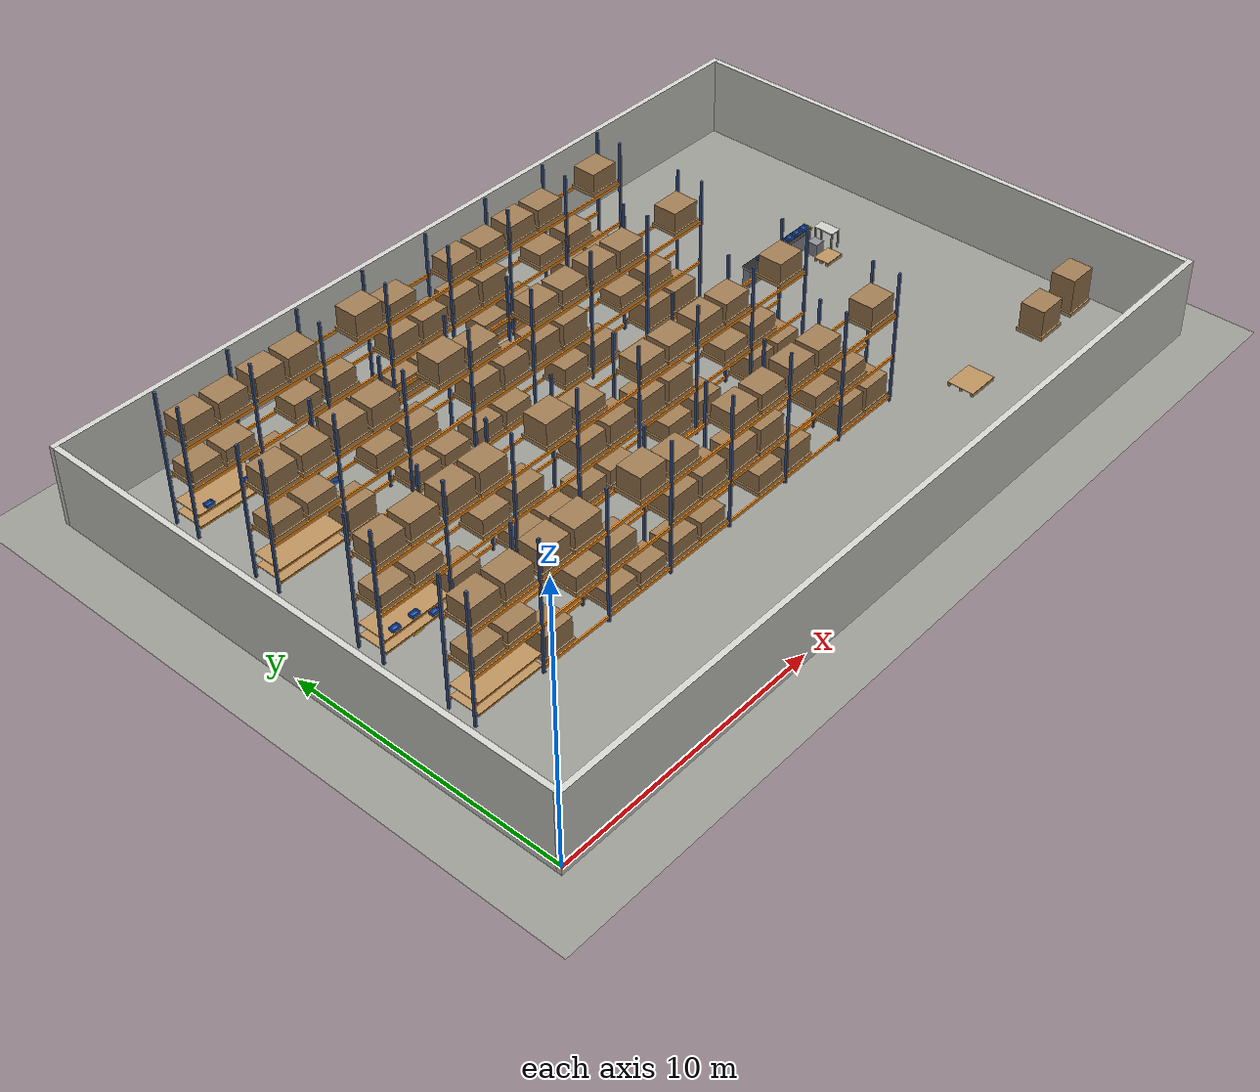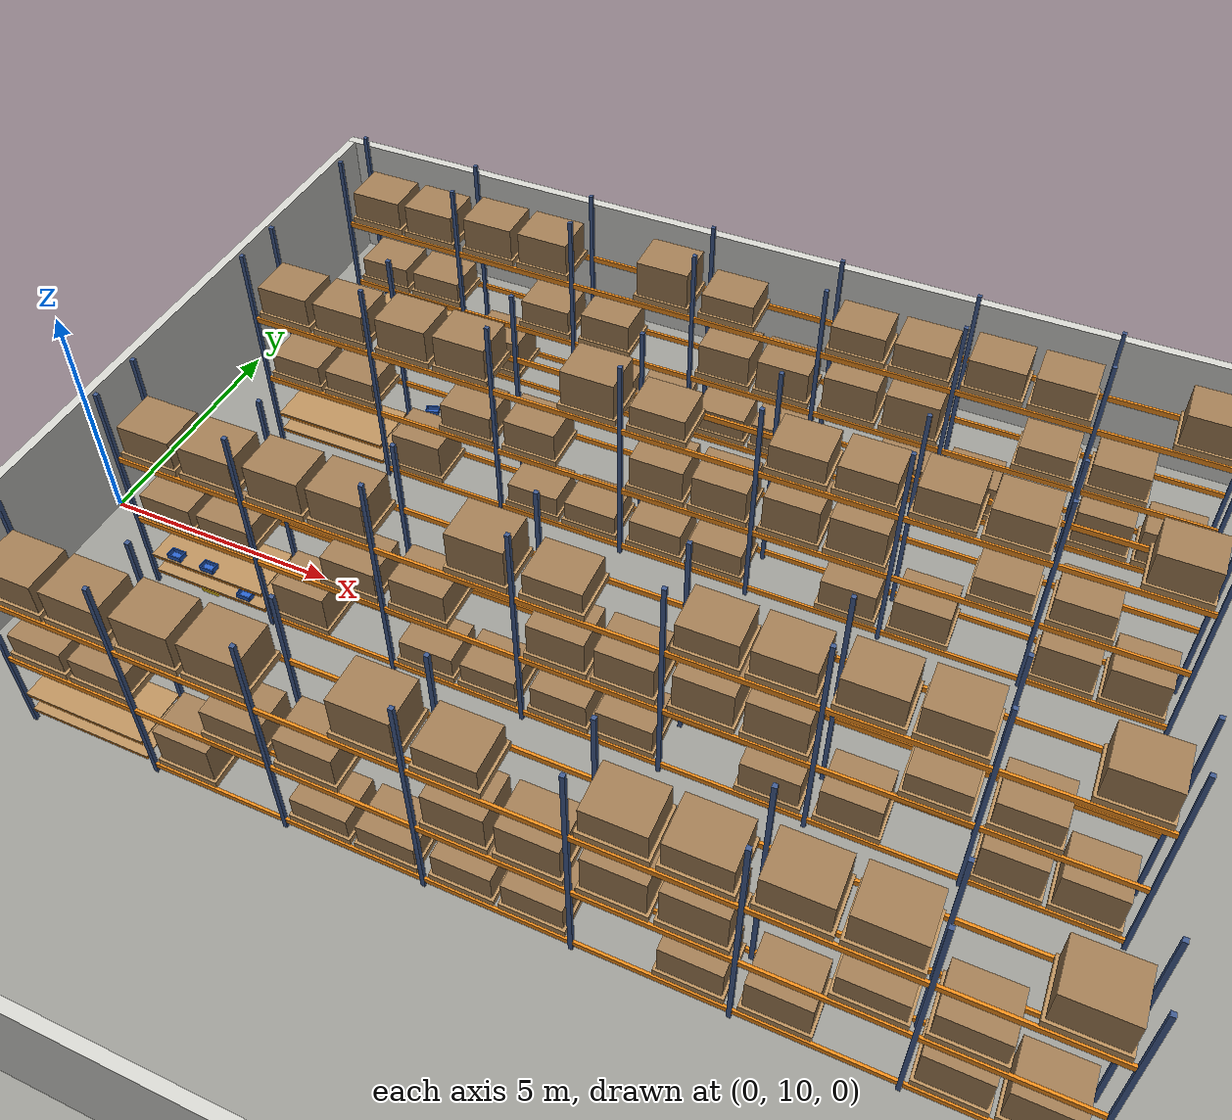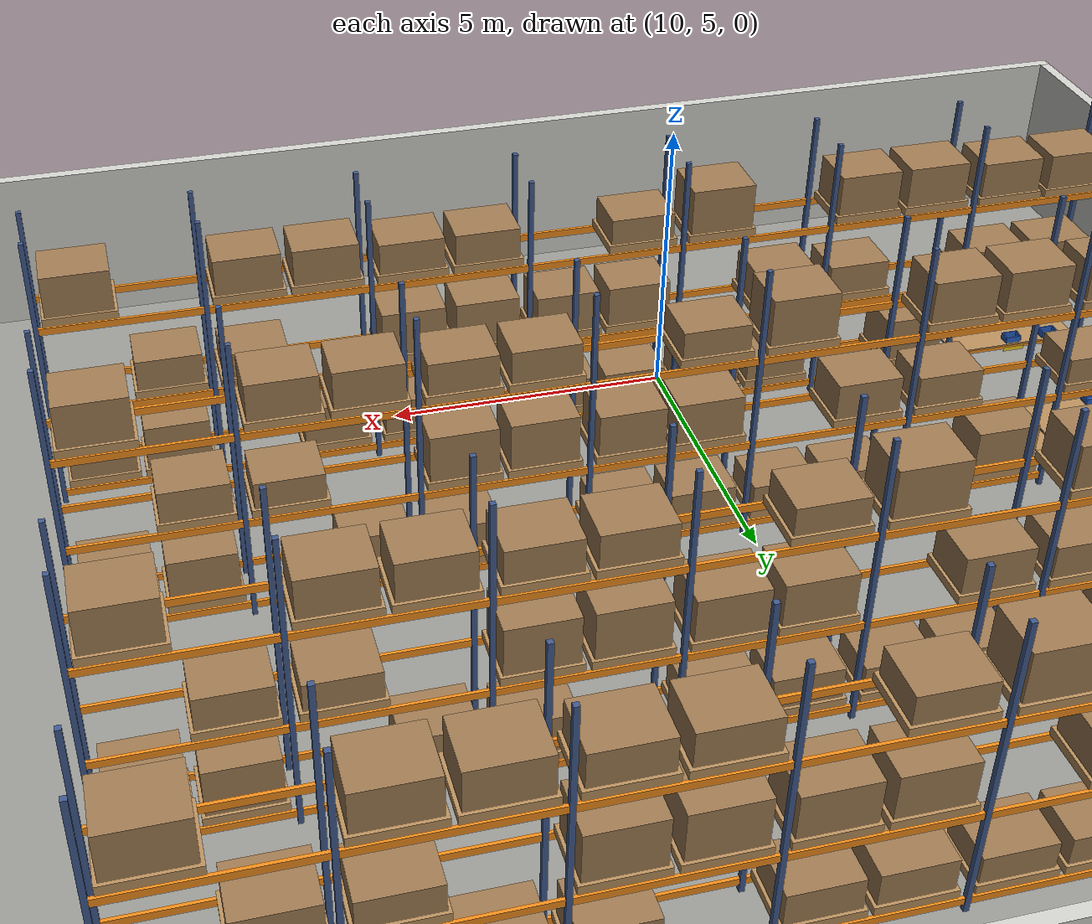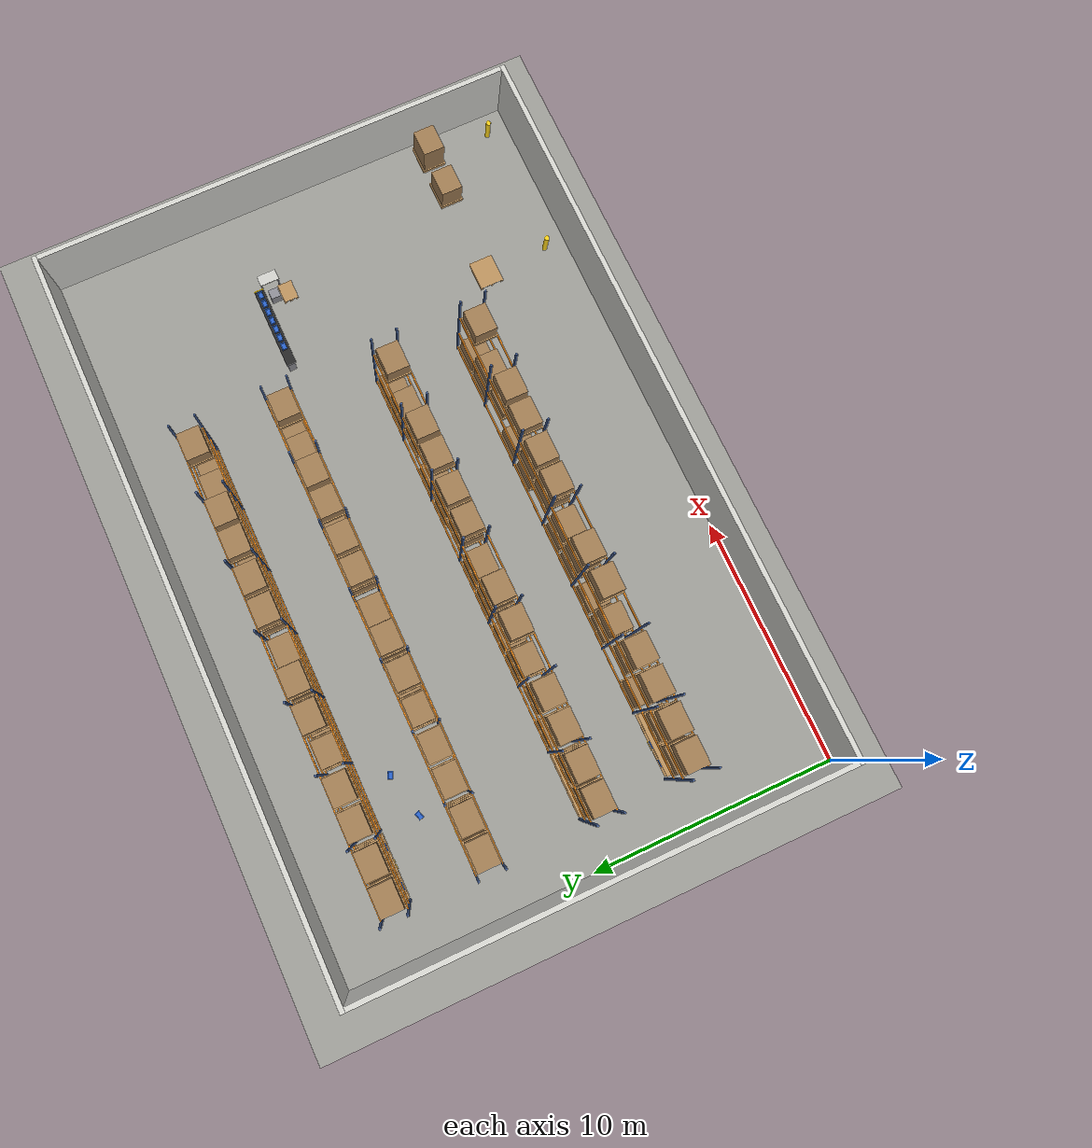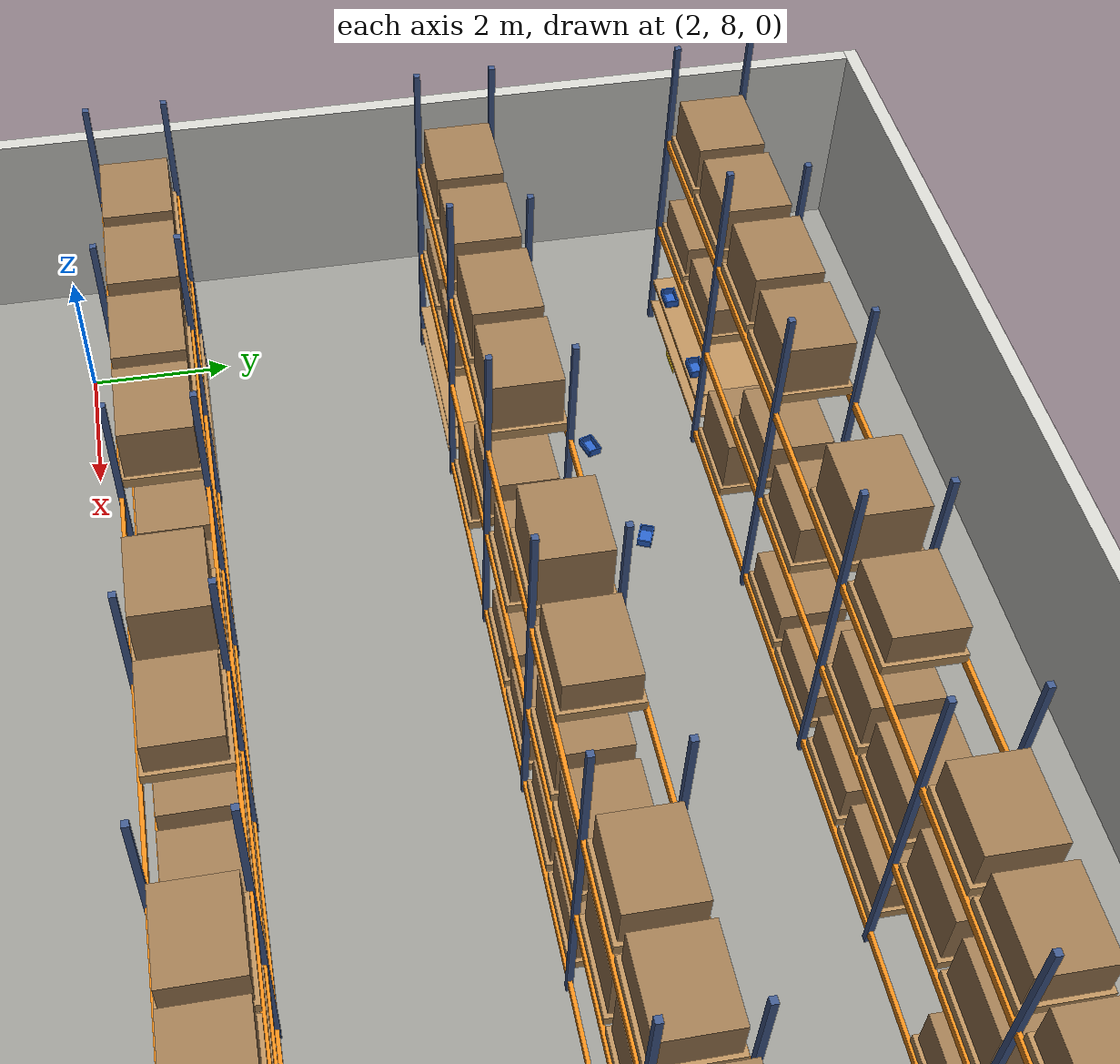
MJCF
<mujoco model="warehouse">
  <compiler angle="radian" />
  <visual>
    <global offwidth="1280" offheight="960" />
    <headlight diffuse="0.5 0.5 0.5" ambient="0.3 0.3 0.3" specular="0 0 0" />
    <quality shadowsize="4096" />
  </visual>
  <asset>
    <texture name="wh_floor" type="2d" builtin="checker" rgb1="0.62 0.62 0.6" rgb2="0.58 0.58 0.56" width="512" height="512" />
    <material name="wh_floor" texture="wh_floor" texrepeat="60 40" reflectance="0.05" />
    <texture name="wh_sky" type="skybox" builtin="gradient" rgb1="0.86 0.88 0.9" rgb2="0.55 0.58 0.62" width="256" height="256" />
    <material name="wh_steel" rgba="0.25 0.35 0.55 1" />
    <material name="wh_beam" rgba="0.95 0.55 0.1 1" />
    <material name="wh_wood" rgba="0.72 0.56 0.36 1" />
    <material name="wh_belt" rgba="0.15 0.15 0.15 1" />
    <material name="wh_frame" rgba="0.55 0.55 0.58 1" />
    <material name="wh_tote" rgba="0.16 0.38 0.78 1" />
    <material name="wh_table" rgba="0.8 0.8 0.78 1" />
    <material name="wh_mark" rgba="0.95 0.8 0.1 1" />
    <material name="wh_load" rgba="0.62 0.48 0.32 1" />
    <material name="wh_wall" rgba="0.82 0.82 0.8 1" />
  </asset>
  <worldbody>
    <light name="wh_sun" pos="15.0 10.0 8" dir="0 0 -1" directional="true" diffuse="0.7 0.7 0.7" />
    <light name="wh_fill" pos="15.0 -4 6" dir="0 0.6 -0.8" diffuse="0.3 0.3 0.3" />
    <geom name="floor" type="plane" size="17.0 12.0 0.05" pos="15.0 10.0 0" material="wh_floor" />
    <camera name="overview" pos="15.0 -6 18" xyaxes="1 0 0 0 0.85 0.53" fovy="60" />
    <camera name="cam1" pos="0.35 0.35 6" xyaxes="0.4889 -0.8723 0 0.2751 0.1542 0.949" fovy="67.7" />
    <camera name="cam2" pos="29.65 19.65 6" xyaxes="-0.6492 0.7606 0 -0.2117 -0.1807 0.9605" fovy="67.7" />
    <camera name="cam3" pos="0.35 19.65 6" xyaxes="-0.6561 -0.7547 0 0.3445 -0.2995 0.8898" fovy="67.7" />
    <camera name="cam4" pos="29.7 9.5 4.5" xyaxes="0.5599 0.8286 0 -0.5287 0.3572 0.77" fovy="50.5" />
    <camera name="cam5" pos="29.65 0.35 5" xyaxes="0.592 0.806 0 -0.4285 0.3147 0.847" fovy="67.7" />
    <camera name="cam6" pos="0.3 15.35 3.5" xyaxes="0 -1 0 0.2955 0 0.9554" fovy="67.7" />
    <geom name="wall_s" type="box" pos="15 -0.1 1.5" size="15.2 0.1 1.5" material="wh_wall" />
    <geom name="wall_n" type="box" pos="15 20.1 1.5" size="15.2 0.1 1.5" material="wh_wall" />
    <geom name="wall_w" type="box" pos="-0.1 10 1.5" size="0.1 10 1.5" material="wh_wall" />
    <geom name="wall_e" type="box" pos="30.1 10 1.5" size="0.1 10 1.5" material="wh_wall" />
    <geom name="rackA_up0_0" type="box" pos="2 16.64 2.5" size="0.04 0.04 2.5" material="wh_steel" />
    <geom name="rackA_up0_1" type="box" pos="2 17.66 2.5" size="0.04 0.04 2.5" material="wh_steel" />
    <geom name="rackA_up1_0" type="box" pos="4.7 16.64 2.5" size="0.04 0.04 2.5" material="wh_steel" />
    <geom name="rackA_up1_1" type="box" pos="4.7 17.66 2.5" size="0.04 0.04 2.5" material="wh_steel" />
    <geom name="rackA_up2_0" type="box" pos="7.4 16.64 2.5" size="0.04 0.04 2.5" material="wh_steel" />
    <geom name="rackA_up2_1" type="box" pos="7.4 17.66 2.5" size="0.04 0.04 2.5" material="wh_steel" />
    <geom name="rackA_up3_0" type="box" pos="10.1 16.64 2.5" size="0.04 0.04 2.5" material="wh_steel" />
    <geom name="rackA_up3_1" type="box" pos="10.1 17.66 2.5" size="0.04 0.04 2.5" material="wh_steel" />
    <geom name="rackA_up4_0" type="box" pos="12.8 16.64 2.5" size="0.04 0.04 2.5" material="wh_steel" />
    <geom name="rackA_up4_1" type="box" pos="12.8 17.66 2.5" size="0.04 0.04 2.5" material="wh_steel" />
    <geom name="rackA_up5_0" type="box" pos="15.5 16.64 2.5" size="0.04 0.04 2.5" material="wh_steel" />
    <geom name="rackA_up5_1" type="box" pos="15.5 17.66 2.5" size="0.04 0.04 2.5" material="wh_steel" />
    <geom name="rackA_up6_0" type="box" pos="18.2 16.64 2.5" size="0.04 0.04 2.5" material="wh_steel" />
    <geom name="rackA_up6_1" type="box" pos="18.2 17.66 2.5" size="0.04 0.04 2.5" material="wh_steel" />
    <geom name="rackA_up7_0" type="box" pos="20.9 16.64 2.5" size="0.04 0.04 2.5" material="wh_steel" />
    <geom name="rackA_up7_1" type="box" pos="20.9 17.66 2.5" size="0.04 0.04 2.5" material="wh_steel" />
    <geom name="rackA_beam0_1_0" type="box" pos="6.05 16.64 0.19" size="1.31 0.025 0.06" material="wh_beam" />
    <geom name="rackA_beam0_1_1" type="box" pos="6.05 17.66 0.19" size="1.31 0.025 0.06" material="wh_beam" />
    <geom name="rackA_beam0_2_0" type="box" pos="8.75 16.64 0.19" size="1.31 0.025 0.06" material="wh_beam" />
    <geom name="rackA_beam0_2_1" type="box" pos="8.75 17.66 0.19" size="1.31 0.025 0.06" material="wh_beam" />
    <geom name="rackA_beam0_3_0" type="box" pos="11.45 16.64 0.19" size="1.31 0.025 0.06" material="wh_beam" />
    <geom name="rackA_beam0_3_1" type="box" pos="11.45 17.66 0.19" size="1.31 0.025 0.06" material="wh_beam" />
    <geom name="rackA_beam0_4_0" type="box" pos="14.15 16.64 0.19" size="1.31 0.025 0.06" material="wh_beam" />
    <geom name="rackA_beam0_4_1" type="box" pos="14.15 17.66 0.19" size="1.31 0.025 0.06" material="wh_beam" />
    <geom name="rackA_beam0_5_0" type="box" pos="16.85 16.64 0.19" size="1.31 0.025 0.06" material="wh_beam" />
    <geom name="rackA_beam0_5_1" type="box" pos="16.85 17.66 0.19" size="1.31 0.025 0.06" material="wh_beam" />
    <geom name="rackA_beam0_6_0" type="box" pos="19.55 16.64 0.19" size="1.31 0.025 0.06" material="wh_beam" />
    <geom name="rackA_beam0_6_1" type="box" pos="19.55 17.66 0.19" size="1.31 0.025 0.06" material="wh_beam" />
    <geom name="rackA_beam1_0_0" type="box" pos="3.35 16.64 1.79" size="1.31 0.025 0.06" material="wh_beam" />
    <geom name="rackA_beam1_0_1" type="box" pos="3.35 17.66 1.79" size="1.31 0.025 0.06" material="wh_beam" />
    <geom name="rackA_beam1_1_0" type="box" pos="6.05 16.64 1.79" size="1.31 0.025 0.06" material="wh_beam" />
    <geom name="rackA_beam1_1_1" type="box" pos="6.05 17.66 1.79" size="1.31 0.025 0.06" material="wh_beam" />
    <geom name="rackA_beam1_2_0" type="box" pos="8.75 16.64 1.79" size="1.31 0.025 0.06" material="wh_beam" />
    <geom name="rackA_beam1_2_1" type="box" pos="8.75 17.66 1.79" size="1.31 0.025 0.06" material="wh_beam" />
    <geom name="rackA_beam1_3_0" type="box" pos="11.45 16.64 1.79" size="1.31 0.025 0.06" material="wh_beam" />
    <geom name="rackA_beam1_3_1" type="box" pos="11.45 17.66 1.79" size="1.31 0.025 0.06" material="wh_beam" />
    <geom name="rackA_beam1_4_0" type="box" pos="14.15 16.64 1.79" size="1.31 0.025 0.06" material="wh_beam" />
    <geom name="rackA_beam1_4_1" type="box" pos="14.15 17.66 1.79" size="1.31 0.025 0.06" material="wh_beam" />
    <geom name="rackA_beam1_5_0" type="box" pos="16.85 16.64 1.79" size="1.31 0.025 0.06" material="wh_beam" />
    <geom name="rackA_beam1_5_1" type="box" pos="16.85 17.66 1.79" size="1.31 0.025 0.06" material="wh_beam" />
    <geom name="rackA_beam1_6_0" type="box" pos="19.55 16.64 1.79" size="1.31 0.025 0.06" material="wh_beam" />
    <geom name="rackA_beam1_6_1" type="box" pos="19.55 17.66 1.79" size="1.31 0.025 0.06" material="wh_beam" />
    <geom name="rackA_beam2_0_0" type="box" pos="3.35 16.64 3.39" size="1.31 0.025 0.06" material="wh_beam" />
    <geom name="rackA_beam2_0_1" type="box" pos="3.35 17.66 3.39" size="1.31 0.025 0.06" material="wh_beam" />
    <geom name="rackA_beam2_1_0" type="box" pos="6.05 16.64 3.39" size="1.31 0.025 0.06" material="wh_beam" />
    <geom name="rackA_beam2_1_1" type="box" pos="6.05 17.66 3.39" size="1.31 0.025 0.06" material="wh_beam" />
    <geom name="rackA_beam2_2_0" type="box" pos="8.75 16.64 3.39" size="1.31 0.025 0.06" material="wh_beam" />
    <geom name="rackA_beam2_2_1" type="box" pos="8.75 17.66 3.39" size="1.31 0.025 0.06" material="wh_beam" />
    <geom name="rackA_beam2_3_0" type="box" pos="11.45 16.64 3.39" size="1.31 0.025 0.06" material="wh_beam" />
    <geom name="rackA_beam2_3_1" type="box" pos="11.45 17.66 3.39" size="1.31 0.025 0.06" material="wh_beam" />
    <geom name="rackA_beam2_4_0" type="box" pos="14.15 16.64 3.39" size="1.31 0.025 0.06" material="wh_beam" />
    <geom name="rackA_beam2_4_1" type="box" pos="14.15 17.66 3.39" size="1.31 0.025 0.06" material="wh_beam" />
    <geom name="rackA_beam2_5_0" type="box" pos="16.85 16.64 3.39" size="1.31 0.025 0.06" material="wh_beam" />
    <geom name="rackA_beam2_5_1" type="box" pos="16.85 17.66 3.39" size="1.31 0.025 0.06" material="wh_beam" />
    <geom name="rackA_beam2_6_0" type="box" pos="19.55 16.64 3.39" size="1.31 0.025 0.06" material="wh_beam" />
    <geom name="rackA_beam2_6_1" type="box" pos="19.55 17.66 3.39" size="1.31 0.025 0.06" material="wh_beam" />
    <geom name="rackA_pal0_0" type="box" pos="2.71 17.15 1.92" size="0.6 0.5 0.07" material="wh_wood" />
    <geom name="rackA_load0_0" type="box" pos="2.71 17.15 2.215" size="0.55 0.45 0.225" material="wh_load" />
    <geom name="rackA_pal0_1" type="box" pos="3.99 17.15 1.92" size="0.6 0.5 0.07" material="wh_wood" />
    <geom name="rackA_load0_1" type="box" pos="3.99 17.15 2.215" size="0.55 0.45 0.225" material="wh_load" />
    <geom name="rackA_pal1_0" type="box" pos="2.71 17.15 3.52" size="0.6 0.5 0.07" material="wh_wood" />
    <geom name="rackA_load1_0" type="box" pos="2.71 17.15 3.9025" size="0.55 0.45 0.3125" material="wh_load" />
    <geom name="rackA_pal1_1" type="box" pos="3.99 17.15 3.52" size="0.6 0.5 0.07" material="wh_wood" />
    <geom name="rackA_load1_1" type="box" pos="3.99 17.15 3.9025" size="0.55 0.45 0.3125" material="wh_load" />
    <geom name="rackA_pal2_0" type="box" pos="5.41 17.15 0.32" size="0.6 0.5 0.07" material="wh_wood" />
    <geom name="rackA_load2_0" type="box" pos="5.41 17.15 0.79" size="0.55 0.45 0.4" material="wh_load" />
    <geom name="rackA_pal3_1" type="box" pos="6.69 17.15 1.92" size="0.6 0.5 0.07" material="wh_wood" />
    <geom name="rackA_load3_1" type="box" pos="6.69 17.15 2.2588" size="0.55 0.45 0.2687" material="wh_load" />
    <geom name="rackA_pal4_0" type="box" pos="5.41 17.15 3.52" size="0.6 0.5 0.07" material="wh_wood" />
    <geom name="rackA_load4_0" type="box" pos="5.41 17.15 3.9463" size="0.55 0.45 0.3562" material="wh_load" />
    <geom name="rackA_pal4_1" type="box" pos="6.69 17.15 3.52" size="0.6 0.5 0.07" material="wh_wood" />
    <geom name="rackA_load4_1" type="box" pos="6.69 17.15 3.9463" size="0.55 0.45 0.3562" material="wh_load" />
    <geom name="rackA_pal5_0" type="box" pos="8.11 17.15 0.32" size="0.6 0.5 0.07" material="wh_wood" />
    <geom name="rackA_load5_0" type="box" pos="8.11 17.15 0.615" size="0.55 0.45 0.225" material="wh_load" />
    <geom name="rackA_pal5_1" type="box" pos="9.39 17.15 0.32" size="0.6 0.5 0.07" material="wh_wood" />
    <geom name="rackA_load5_1" type="box" pos="9.39 17.15 0.615" size="0.55 0.45 0.225" material="wh_load" />
    <geom name="rackA_pal6_0" type="box" pos="8.11 17.15 1.92" size="0.6 0.5 0.07" material="wh_wood" />
    <geom name="rackA_load6_0" type="box" pos="8.11 17.15 2.3025" size="0.55 0.45 0.3125" material="wh_load" />
    <geom name="rackA_pal7_1" type="box" pos="9.39 17.15 3.52" size="0.6 0.5 0.07" material="wh_wood" />
    <geom name="rackA_load7_1" type="box" pos="9.39 17.15 3.99" size="0.55 0.45 0.4" material="wh_load" />
    <geom name="rackA_pal8_0" type="box" pos="10.81 17.15 0.32" size="0.6 0.5 0.07" material="wh_wood" />
    <geom name="rackA_load8_0" type="box" pos="10.81 17.15 0.6587" size="0.55 0.45 0.2687" material="wh_load" />
    <geom name="rackA_pal8_1" type="box" pos="12.09 17.15 0.32" size="0.6 0.5 0.07" material="wh_wood" />
    <geom name="rackA_load8_1" type="box" pos="12.09 17.15 0.6587" size="0.55 0.45 0.2687" material="wh_load" />
    <geom name="rackA_pal9_0" type="box" pos="10.81 17.15 1.92" size="0.6 0.5 0.07" material="wh_wood" />
    <geom name="rackA_load9_0" type="box" pos="10.81 17.15 2.3463" size="0.55 0.45 0.3562" material="wh_load" />
    <geom name="rackA_pal9_1" type="box" pos="12.09 17.15 1.92" size="0.6 0.5 0.07" material="wh_wood" />
    <geom name="rackA_load9_1" type="box" pos="12.09 17.15 2.3463" size="0.55 0.45 0.3562" material="wh_load" />
    <geom name="rackA_pal10_0" type="box" pos="10.81 17.15 3.52" size="0.6 0.5 0.07" material="wh_wood" />
    <geom name="rackA_load10_0" type="box" pos="10.81 17.15 3.815" size="0.55 0.45 0.225" material="wh_load" />
    <geom name="rackA_pal11_1" type="box" pos="14.79 17.15 0.32" size="0.6 0.5 0.07" material="wh_wood" />
    <geom name="rackA_load11_1" type="box" pos="14.79 17.15 0.7025" size="0.55 0.45 0.3125" material="wh_load" />
    <geom name="rackA_pal12_0" type="box" pos="13.51 17.15 1.92" size="0.6 0.5 0.07" material="wh_wood" />
    <geom name="rackA_load12_0" type="box" pos="13.51 17.15 2.39" size="0.55 0.45 0.4" material="wh_load" />
    <geom name="rackA_pal12_1" type="box" pos="14.79 17.15 1.92" size="0.6 0.5 0.07" material="wh_wood" />
    <geom name="rackA_load12_1" type="box" pos="14.79 17.15 2.39" size="0.55 0.45 0.4" material="wh_load" />
    <geom name="rackA_pal13_0" type="box" pos="13.51 17.15 3.52" size="0.6 0.5 0.07" material="wh_wood" />
    <geom name="rackA_load13_0" type="box" pos="13.51 17.15 3.8588" size="0.55 0.45 0.2687" material="wh_load" />
    <geom name="rackA_pal13_1" type="box" pos="14.79 17.15 3.52" size="0.6 0.5 0.07" material="wh_wood" />
    <geom name="rackA_load13_1" type="box" pos="14.79 17.15 3.8588" size="0.55 0.45 0.2687" material="wh_load" />
    <geom name="rackA_pal14_0" type="box" pos="16.21 17.15 0.32" size="0.6 0.5 0.07" material="wh_wood" />
    <geom name="rackA_load14_0" type="box" pos="16.21 17.15 0.7462" size="0.55 0.45 0.3562" material="wh_load" />
    <geom name="rackA_pal15_1" type="box" pos="17.49 17.15 1.92" size="0.6 0.5 0.07" material="wh_wood" />
    <geom name="rackA_load15_1" type="box" pos="17.49 17.15 2.215" size="0.55 0.45 0.225" material="wh_load" />
    <geom name="rackA_pal16_0" type="box" pos="16.21 17.15 3.52" size="0.6 0.5 0.07" material="wh_wood" />
    <geom name="rackA_load16_0" type="box" pos="16.21 17.15 3.9025" size="0.55 0.45 0.3125" material="wh_load" />
    <geom name="rackA_pal16_1" type="box" pos="17.49 17.15 3.52" size="0.6 0.5 0.07" material="wh_wood" />
    <geom name="rackA_load16_1" type="box" pos="17.49 17.15 3.9025" size="0.55 0.45 0.3125" material="wh_load" />
    <geom name="rackA_pal17_0" type="box" pos="18.91 17.15 0.32" size="0.6 0.5 0.07" material="wh_wood" />
    <geom name="rackA_load17_0" type="box" pos="18.91 17.15 0.79" size="0.55 0.45 0.4" material="wh_load" />
    <geom name="rackA_pal17_1" type="box" pos="20.19 17.15 0.32" size="0.6 0.5 0.07" material="wh_wood" />
    <geom name="rackA_load17_1" type="box" pos="20.19 17.15 0.79" size="0.55 0.45 0.4" material="wh_load" />
    <geom name="rackA_pal18_0" type="box" pos="18.91 17.15 1.92" size="0.6 0.5 0.07" material="wh_wood" />
    <geom name="rackA_load18_0" type="box" pos="18.91 17.15 2.2588" size="0.55 0.45 0.2687" material="wh_load" />
    <geom name="rackA_pal19_1" type="box" pos="20.19 17.15 3.52" size="0.6 0.5 0.07" material="wh_wood" />
    <geom name="rackA_load19_1" type="box" pos="20.19 17.15 3.9463" size="0.55 0.45 0.3562" material="wh_load" />
    <geom name="rackB_up0_0" type="box" pos="2 13.04 2.5" size="0.04 0.04 2.5" material="wh_steel" />
    <geom name="rackB_up0_1" type="box" pos="2 14.06 2.5" size="0.04 0.04 2.5" material="wh_steel" />
    <geom name="rackB_up1_0" type="box" pos="4.7 13.04 2.5" size="0.04 0.04 2.5" material="wh_steel" />
    <geom name="rackB_up1_1" type="box" pos="4.7 14.06 2.5" size="0.04 0.04 2.5" material="wh_steel" />
    <geom name="rackB_up2_0" type="box" pos="7.4 13.04 2.5" size="0.04 0.04 2.5" material="wh_steel" />
    <geom name="rackB_up2_1" type="box" pos="7.4 14.06 2.5" size="0.04 0.04 2.5" material="wh_steel" />
    <geom name="rackB_up3_0" type="box" pos="10.1 13.04 2.5" size="0.04 0.04 2.5" material="wh_steel" />
    <geom name="rackB_up3_1" type="box" pos="10.1 14.06 2.5" size="0.04 0.04 2.5" material="wh_steel" />
    <geom name="rackB_up4_0" type="box" pos="12.8 13.04 2.5" size="0.04 0.04 2.5" material="wh_steel" />
    <geom name="rackB_up4_1" type="box" pos="12.8 14.06 2.5" size="0.04 0.04 2.5" material="wh_steel" />
    <geom name="rackB_up5_0" type="box" pos="15.5 13.04 2.5" size="0.04 0.04 2.5" material="wh_steel" />
    <geom name="rackB_up5_1" type="box" pos="15.5 14.06 2.5" size="0.04 0.04 2.5" material="wh_steel" />
    <geom name="rackB_up6_0" type="box" pos="18.2 13.04 2.5" size="0.04 0.04 2.5" material="wh_steel" />
    <geom name="rackB_up6_1" type="box" pos="18.2 14.06 2.5" size="0.04 0.04 2.5" material="wh_steel" />
    <geom name="rackB_up7_0" type="box" pos="20.9 13.04 2.5" size="0.04 0.04 2.5" material="wh_steel" />
    <geom name="rackB_up7_1" type="box" pos="20.9 14.06 2.5" size="0.04 0.04 2.5" material="wh_steel" />
    <geom name="rackB_beam0_1_0" type="box" pos="6.05 13.04 0.19" size="1.31 0.025 0.06" material="wh_beam" />
    <geom name="rackB_beam0_1_1" type="box" pos="6.05 14.06 0.19" size="1.31 0.025 0.06" material="wh_beam" />
    <geom name="rackB_beam0_2_0" type="box" pos="8.75 13.04 0.19" size="1.31 0.025 0.06" material="wh_beam" />
    <geom name="rackB_beam0_2_1" type="box" pos="8.75 14.06 0.19" size="1.31 0.025 0.06" material="wh_beam" />
    <geom name="rackB_beam0_3_0" type="box" pos="11.45 13.04 0.19" size="1.31 0.025 0.06" material="wh_beam" />
    <geom name="rackB_beam0_3_1" type="box" pos="11.45 14.06 0.19" size="1.31 0.025 0.06" material="wh_beam" />
    <geom name="rackB_beam0_4_0" type="box" pos="14.15 13.04 0.19" size="1.31 0.025 0.06" material="wh_beam" />
    <geom name="rackB_beam0_4_1" type="box" pos="14.15 14.06 0.19" size="1.31 0.025 0.06" material="wh_beam" />
    <geom name="rackB_beam0_5_0" type="box" pos="16.85 13.04 0.19" size="1.31 0.025 0.06" material="wh_beam" />
    <geom name="rackB_beam0_5_1" type="box" pos="16.85 14.06 0.19" size="1.31 0.025 0.06" material="wh_beam" />
    <geom name="rackB_beam0_6_0" type="box" pos="19.55 13.04 0.19" size="1.31 0.025 0.06" material="wh_beam" />
    <geom name="rackB_beam0_6_1" type="box" pos="19.55 14.06 0.19" size="1.31 0.025 0.06" material="wh_beam" />
    <geom name="rackB_beam1_0_0" type="box" pos="3.35 13.04 1.79" size="1.31 0.025 0.06" material="wh_beam" />
    <geom name="rackB_beam1_0_1" type="box" pos="3.35 14.06 1.79" size="1.31 0.025 0.06" material="wh_beam" />
    <geom name="rackB_beam1_1_0" type="box" pos="6.05 13.04 1.79" size="1.31 0.025 0.06" material="wh_beam" />
    <geom name="rackB_beam1_1_1" type="box" pos="6.05 14.06 1.79" size="1.31 0.025 0.06" material="wh_beam" />
    <geom name="rackB_beam1_2_0" type="box" pos="8.75 13.04 1.79" size="1.31 0.025 0.06" material="wh_beam" />
    <geom name="rackB_beam1_2_1" type="box" pos="8.75 14.06 1.79" size="1.31 0.025 0.06" material="wh_beam" />
    <geom name="rackB_beam1_3_0" type="box" pos="11.45 13.04 1.79" size="1.31 0.025 0.06" material="wh_beam" />
    <geom name="rackB_beam1_3_1" type="box" pos="11.45 14.06 1.79" size="1.31 0.025 0.06" material="wh_beam" />
    <geom name="rackB_beam1_4_0" type="box" pos="14.15 13.04 1.79" size="1.31 0.025 0.06" material="wh_beam" />
    <geom name="rackB_beam1_4_1" type="box" pos="14.15 14.06 1.79" size="1.31 0.025 0.06" material="wh_beam" />
    <geom name="rackB_beam1_5_0" type="box" pos="16.85 13.04 1.79" size="1.31 0.025 0.06" material="wh_beam" />
    <geom name="rackB_beam1_5_1" type="box" pos="16.85 14.06 1.79" size="1.31 0.025 0.06" material="wh_beam" />
    <geom name="rackB_beam1_6_0" type="box" pos="19.55 13.04 1.79" size="1.31 0.025 0.06" material="wh_beam" />
    <geom name="rackB_beam1_6_1" type="box" pos="19.55 14.06 1.79" size="1.31 0.025 0.06" material="wh_beam" />
    <geom name="rackB_beam2_0_0" type="box" pos="3.35 13.04 3.39" size="1.31 0.025 0.06" material="wh_beam" />
    <geom name="rackB_beam2_0_1" type="box" pos="3.35 14.06 3.39" size="1.31 0.025 0.06" material="wh_beam" />
    <geom name="rackB_beam2_1_0" type="box" pos="6.05 13.04 3.39" size="1.31 0.025 0.06" material="wh_beam" />
    <geom name="rackB_beam2_1_1" type="box" pos="6.05 14.06 3.39" size="1.31 0.025 0.06" material="wh_beam" />
    <geom name="rackB_beam2_2_0" type="box" pos="8.75 13.04 3.39" size="1.31 0.025 0.06" material="wh_beam" />
    <geom name="rackB_beam2_2_1" type="box" pos="8.75 14.06 3.39" size="1.31 0.025 0.06" material="wh_beam" />
    <geom name="rackB_beam2_3_0" type="box" pos="11.45 13.04 3.39" size="1.31 0.025 0.06" material="wh_beam" />
    <geom name="rackB_beam2_3_1" type="box" pos="11.45 14.06 3.39" size="1.31 0.025 0.06" material="wh_beam" />
    <geom name="rackB_beam2_4_0" type="box" pos="14.15 13.04 3.39" size="1.31 0.025 0.06" material="wh_beam" />
    <geom name="rackB_beam2_4_1" type="box" pos="14.15 14.06 3.39" size="1.31 0.025 0.06" material="wh_beam" />
    <geom name="rackB_beam2_5_0" type="box" pos="16.85 13.04 3.39" size="1.31 0.025 0.06" material="wh_beam" />
    <geom name="rackB_beam2_5_1" type="box" pos="16.85 14.06 3.39" size="1.31 0.025 0.06" material="wh_beam" />
    <geom name="rackB_beam2_6_0" type="box" pos="19.55 13.04 3.39" size="1.31 0.025 0.06" material="wh_beam" />
    <geom name="rackB_beam2_6_1" type="box" pos="19.55 14.06 3.39" size="1.31 0.025 0.06" material="wh_beam" />
    <geom name="rackB_pal0_0" type="box" pos="2.71 13.55 1.92" size="0.6 0.5 0.07" material="wh_wood" />
    <geom name="rackB_load0_0" type="box" pos="2.71 13.55 2.215" size="0.55 0.45 0.225" material="wh_load" />
    <geom name="rackB_pal0_1" type="box" pos="3.99 13.55 1.92" size="0.6 0.5 0.07" material="wh_wood" />
    <geom name="rackB_load0_1" type="box" pos="3.99 13.55 2.215" size="0.55 0.45 0.225" material="wh_load" />
    <geom name="rackB_pal1_0" type="box" pos="2.71 13.55 3.52" size="0.6 0.5 0.07" material="wh_wood" />
    <geom name="rackB_load1_0" type="box" pos="2.71 13.55 3.9025" size="0.55 0.45 0.3125" material="wh_load" />
    <geom name="rackB_pal1_1" type="box" pos="3.99 13.55 3.52" size="0.6 0.5 0.07" material="wh_wood" />
    <geom name="rackB_load1_1" type="box" pos="3.99 13.55 3.9025" size="0.55 0.45 0.3125" material="wh_load" />
    <geom name="rackB_pal2_0" type="box" pos="5.41 13.55 0.32" size="0.6 0.5 0.07" material="wh_wood" />
    <geom name="rackB_load2_0" type="box" pos="5.41 13.55 0.79" size="0.55 0.45 0.4" material="wh_load" />
    <geom name="rackB_pal3_1" type="box" pos="6.69 13.55 1.92" size="0.6 0.5 0.07" material="wh_wood" />
    <geom name="rackB_load3_1" type="box" pos="6.69 13.55 2.2588" size="0.55 0.45 0.2687" material="wh_load" />
    <geom name="rackB_pal4_0" type="box" pos="5.41 13.55 3.52" size="0.6 0.5 0.07" material="wh_wood" />
    <geom name="rackB_load4_0" type="box" pos="5.41 13.55 3.9463" size="0.55 0.45 0.3562" material="wh_load" />
    <geom name="rackB_pal4_1" type="box" pos="6.69 13.55 3.52" size="0.6 0.5 0.07" material="wh_wood" />
    <geom name="rackB_load4_1" type="box" pos="6.69 13.55 3.9463" size="0.55 0.45 0.3562" material="wh_load" />
    <geom name="rackB_pal5_0" type="box" pos="8.11 13.55 0.32" size="0.6 0.5 0.07" material="wh_wood" />
    <geom name="rackB_load5_0" type="box" pos="8.11 13.55 0.615" size="0.55 0.45 0.225" material="wh_load" />
    <geom name="rackB_pal5_1" type="box" pos="9.39 13.55 0.32" size="0.6 0.5 0.07" material="wh_wood" />
    <geom name="rackB_load5_1" type="box" pos="9.39 13.55 0.615" size="0.55 0.45 0.225" material="wh_load" />
    <geom name="rackB_pal6_0" type="box" pos="8.11 13.55 1.92" size="0.6 0.5 0.07" material="wh_wood" />
    <geom name="rackB_load6_0" type="box" pos="8.11 13.55 2.3025" size="0.55 0.45 0.3125" material="wh_load" />
    <geom name="rackB_pal7_1" type="box" pos="9.39 13.55 3.52" size="0.6 0.5 0.07" material="wh_wood" />
    <geom name="rackB_load7_1" type="box" pos="9.39 13.55 3.99" size="0.55 0.45 0.4" material="wh_load" />
    <geom name="rackB_pal8_0" type="box" pos="10.81 13.55 0.32" size="0.6 0.5 0.07" material="wh_wood" />
    <geom name="rackB_load8_0" type="box" pos="10.81 13.55 0.6587" size="0.55 0.45 0.2687" material="wh_load" />
    <geom name="rackB_pal8_1" type="box" pos="12.09 13.55 0.32" size="0.6 0.5 0.07" material="wh_wood" />
    <geom name="rackB_load8_1" type="box" pos="12.09 13.55 0.6587" size="0.55 0.45 0.2687" material="wh_load" />
    <geom name="rackB_pal9_0" type="box" pos="10.81 13.55 1.92" size="0.6 0.5 0.07" material="wh_wood" />
    <geom name="rackB_load9_0" type="box" pos="10.81 13.55 2.3463" size="0.55 0.45 0.3562" material="wh_load" />
    <geom name="rackB_pal9_1" type="box" pos="12.09 13.55 1.92" size="0.6 0.5 0.07" material="wh_wood" />
    <geom name="rackB_load9_1" type="box" pos="12.09 13.55 2.3463" size="0.55 0.45 0.3562" material="wh_load" />
    <geom name="rackB_pal10_0" type="box" pos="10.81 13.55 3.52" size="0.6 0.5 0.07" material="wh_wood" />
    <geom name="rackB_load10_0" type="box" pos="10.81 13.55 3.815" size="0.55 0.45 0.225" material="wh_load" />
    <geom name="rackB_pal11_1" type="box" pos="14.79 13.55 0.32" size="0.6 0.5 0.07" material="wh_wood" />
    <geom name="rackB_load11_1" type="box" pos="14.79 13.55 0.7025" size="0.55 0.45 0.3125" material="wh_load" />
    <geom name="rackB_pal12_0" type="box" pos="13.51 13.55 1.92" size="0.6 0.5 0.07" material="wh_wood" />
    <geom name="rackB_load12_0" type="box" pos="13.51 13.55 2.39" size="0.55 0.45 0.4" material="wh_load" />
    <geom name="rackB_pal12_1" type="box" pos="14.79 13.55 1.92" size="0.6 0.5 0.07" material="wh_wood" />
    <geom name="rackB_load12_1" type="box" pos="14.79 13.55 2.39" size="0.55 0.45 0.4" material="wh_load" />
    <geom name="rackB_pal13_0" type="box" pos="13.51 13.55 3.52" size="0.6 0.5 0.07" material="wh_wood" />
    <geom name="rackB_load13_0" type="box" pos="13.51 13.55 3.8588" size="0.55 0.45 0.2687" material="wh_load" />
    <geom name="rackB_pal13_1" type="box" pos="14.79 13.55 3.52" size="0.6 0.5 0.07" material="wh_wood" />
    <geom name="rackB_load13_1" type="box" pos="14.79 13.55 3.8588" size="0.55 0.45 0.2687" material="wh_load" />
    <geom name="rackB_pal14_0" type="box" pos="16.21 13.55 0.32" size="0.6 0.5 0.07" material="wh_wood" />
    <geom name="rackB_load14_0" type="box" pos="16.21 13.55 0.7462" size="0.55 0.45 0.3562" material="wh_load" />
    <geom name="rackB_pal15_1" type="box" pos="17.49 13.55 1.92" size="0.6 0.5 0.07" material="wh_wood" />
    <geom name="rackB_load15_1" type="box" pos="17.49 13.55 2.215" size="0.55 0.45 0.225" material="wh_load" />
    <geom name="rackB_pal16_0" type="box" pos="16.21 13.55 3.52" size="0.6 0.5 0.07" material="wh_wood" />
    <geom name="rackB_load16_0" type="box" pos="16.21 13.55 3.9025" size="0.55 0.45 0.3125" material="wh_load" />
    <geom name="rackB_pal16_1" type="box" pos="17.49 13.55 3.52" size="0.6 0.5 0.07" material="wh_wood" />
    <geom name="rackB_load16_1" type="box" pos="17.49 13.55 3.9025" size="0.55 0.45 0.3125" material="wh_load" />
    <geom name="rackB_pal17_0" type="box" pos="18.91 13.55 0.32" size="0.6 0.5 0.07" material="wh_wood" />
    <geom name="rackB_load17_0" type="box" pos="18.91 13.55 0.79" size="0.55 0.45 0.4" material="wh_load" />
    <geom name="rackB_pal17_1" type="box" pos="20.19 13.55 0.32" size="0.6 0.5 0.07" material="wh_wood" />
    <geom name="rackB_load17_1" type="box" pos="20.19 13.55 0.79" size="0.55 0.45 0.4" material="wh_load" />
    <geom name="rackB_pal18_0" type="box" pos="18.91 13.55 1.92" size="0.6 0.5 0.07" material="wh_wood" />
    <geom name="rackB_load18_0" type="box" pos="18.91 13.55 2.2588" size="0.55 0.45 0.2687" material="wh_load" />
    <geom name="rackB_pal19_1" type="box" pos="20.19 13.55 3.52" size="0.6 0.5 0.07" material="wh_wood" />
    <geom name="rackB_load19_1" type="box" pos="20.19 13.55 3.9463" size="0.55 0.45 0.3562" material="wh_load" />
    <geom name="rackC_up0_0" type="box" pos="2 8.64 2.5" size="0.04 0.04 2.5" material="wh_steel" />
    <geom name="rackC_up0_1" type="box" pos="2 9.66 2.5" size="0.04 0.04 2.5" material="wh_steel" />
    <geom name="rackC_up1_0" type="box" pos="4.7 8.64 2.5" size="0.04 0.04 2.5" material="wh_steel" />
    <geom name="rackC_up1_1" type="box" pos="4.7 9.66 2.5" size="0.04 0.04 2.5" material="wh_steel" />
    <geom name="rackC_up2_0" type="box" pos="7.4 8.64 2.5" size="0.04 0.04 2.5" material="wh_steel" />
    <geom name="rackC_up2_1" type="box" pos="7.4 9.66 2.5" size="0.04 0.04 2.5" material="wh_steel" />
    <geom name="rackC_up3_0" type="box" pos="10.1 8.64 2.5" size="0.04 0.04 2.5" material="wh_steel" />
    <geom name="rackC_up3_1" type="box" pos="10.1 9.66 2.5" size="0.04 0.04 2.5" material="wh_steel" />
    <geom name="rackC_up4_0" type="box" pos="12.8 8.64 2.5" size="0.04 0.04 2.5" material="wh_steel" />
    <geom name="rackC_up4_1" type="box" pos="12.8 9.66 2.5" size="0.04 0.04 2.5" material="wh_steel" />
    <geom name="rackC_up5_0" type="box" pos="15.5 8.64 2.5" size="0.04 0.04 2.5" material="wh_steel" />
    <geom name="rackC_up5_1" type="box" pos="15.5 9.66 2.5" size="0.04 0.04 2.5" material="wh_steel" />
    <geom name="rackC_up6_0" type="box" pos="18.2 8.64 2.5" size="0.04 0.04 2.5" material="wh_steel" />
    <geom name="rackC_up6_1" type="box" pos="18.2 9.66 2.5" size="0.04 0.04 2.5" material="wh_steel" />
    <geom name="rackC_up7_0" type="box" pos="20.9 8.64 2.5" size="0.04 0.04 2.5" material="wh_steel" />
    <geom name="rackC_up7_1" type="box" pos="20.9 9.66 2.5" size="0.04 0.04 2.5" material="wh_steel" />
    <geom name="rackC_beam0_1_0" type="box" pos="6.05 8.64 0.19" size="1.31 0.025 0.06" material="wh_beam" />
    <geom name="rackC_beam0_1_1" type="box" pos="6.05 9.66 0.19" size="1.31 0.025 0.06" material="wh_beam" />
    <geom name="rackC_beam0_2_0" type="box" pos="8.75 8.64 0.19" size="1.31 0.025 0.06" material="wh_beam" />
    <geom name="rackC_beam0_2_1" type="box" pos="8.75 9.66 0.19" size="1.31 0.025 0.06" material="wh_beam" />
    <geom name="rackC_beam0_3_0" type="box" pos="11.45 8.64 0.19" size="1.31 0.025 0.06" material="wh_beam" />
    <geom name="rackC_beam0_3_1" type="box" pos="11.45 9.66 0.19" size="1.31 0.025 0.06" material="wh_beam" />
    <geom name="rackC_beam0_4_0" type="box" pos="14.15 8.64 0.19" size="1.31 0.025 0.06" material="wh_beam" />
    <geom name="rackC_beam0_4_1" type="box" pos="14.15 9.66 0.19" size="1.31 0.025 0.06" material="wh_beam" />
    <geom name="rackC_beam0_5_0" type="box" pos="16.85 8.64 0.19" size="1.31 0.025 0.06" material="wh_beam" />
    <geom name="rackC_beam0_5_1" type="box" pos="16.85 9.66 0.19" size="1.31 0.025 0.06" material="wh_beam" />
    <geom name="rackC_beam0_6_0" type="box" pos="19.55 8.64 0.19" size="1.31 0.025 0.06" material="wh_beam" />
    <geom name="rackC_beam0_6_1" type="box" pos="19.55 9.66 0.19" size="1.31 0.025 0.06" material="wh_beam" />
    <geom name="rackC_beam1_0_0" type="box" pos="3.35 8.64 1.79" size="1.31 0.025 0.06" material="wh_beam" />
    <geom name="rackC_beam1_0_1" type="box" pos="3.35 9.66 1.79" size="1.31 0.025 0.06" material="wh_beam" />
    <geom name="rackC_beam1_1_0" type="box" pos="6.05 8.64 1.79" size="1.31 0.025 0.06" material="wh_beam" />
    <geom name="rackC_beam1_1_1" type="box" pos="6.05 9.66 1.79" size="1.31 0.025 0.06" material="wh_beam" />
    <geom name="rackC_beam1_2_0" type="box" pos="8.75 8.64 1.79" size="1.31 0.025 0.06" material="wh_beam" />
    <geom name="rackC_beam1_2_1" type="box" pos="8.75 9.66 1.79" size="1.31 0.025 0.06" material="wh_beam" />
    <geom name="rackC_beam1_3_0" type="box" pos="11.45 8.64 1.79" size="1.31 0.025 0.06" material="wh_beam" />
    <geom name="rackC_beam1_3_1" type="box" pos="11.45 9.66 1.79" size="1.31 0.025 0.06" material="wh_beam" />
    <geom name="rackC_beam1_4_0" type="box" pos="14.15 8.64 1.79" size="1.31 0.025 0.06" material="wh_beam" />
    <geom name="rackC_beam1_4_1" type="box" pos="14.15 9.66 1.79" size="1.31 0.025 0.06" material="wh_beam" />
    <geom name="rackC_beam1_5_0" type="box" pos="16.85 8.64 1.79" size="1.31 0.025 0.06" material="wh_beam" />
    <geom name="rackC_beam1_5_1" type="box" pos="16.85 9.66 1.79" size="1.31 0.025 0.06" material="wh_beam" />
    <geom name="rackC_beam1_6_0" type="box" pos="19.55 8.64 1.79" size="1.31 0.025 0.06" material="wh_beam" />
    <geom name="rackC_beam1_6_1" type="box" pos="19.55 9.66 1.79" size="1.31 0.025 0.06" material="wh_beam" />
    <geom name="rackC_beam2_0_0" type="box" pos="3.35 8.64 3.39" size="1.31 0.025 0.06" material="wh_beam" />
    <geom name="rackC_beam2_0_1" type="box" pos="3.35 9.66 3.39" size="1.31 0.025 0.06" material="wh_beam" />
    <geom name="rackC_beam2_1_0" type="box" pos="6.05 8.64 3.39" size="1.31 0.025 0.06" material="wh_beam" />
    <geom name="rackC_beam2_1_1" type="box" pos="6.05 9.66 3.39" size="1.31 0.025 0.06" material="wh_beam" />
    <geom name="rackC_beam2_2_0" type="box" pos="8.75 8.64 3.39" size="1.31 0.025 0.06" material="wh_beam" />
    <geom name="rackC_beam2_2_1" type="box" pos="8.75 9.66 3.39" size="1.31 0.025 0.06" material="wh_beam" />
    <geom name="rackC_beam2_3_0" type="box" pos="11.45 8.64 3.39" size="1.31 0.025 0.06" material="wh_beam" />
    <geom name="rackC_beam2_3_1" type="box" pos="11.45 9.66 3.39" size="1.31 0.025 0.06" material="wh_beam" />
    <geom name="rackC_beam2_4_0" type="box" pos="14.15 8.64 3.39" size="1.31 0.025 0.06" material="wh_beam" />
    <geom name="rackC_beam2_4_1" type="box" pos="14.15 9.66 3.39" size="1.31 0.025 0.06" material="wh_beam" />
    <geom name="rackC_beam2_5_0" type="box" pos="16.85 8.64 3.39" size="1.31 0.025 0.06" material="wh_beam" />
    <geom name="rackC_beam2_5_1" type="box" pos="16.85 9.66 3.39" size="1.31 0.025 0.06" material="wh_beam" />
    <geom name="rackC_beam2_6_0" type="box" pos="19.55 8.64 3.39" size="1.31 0.025 0.06" material="wh_beam" />
    <geom name="rackC_beam2_6_1" type="box" pos="19.55 9.66 3.39" size="1.31 0.025 0.06" material="wh_beam" />
    <geom name="rackC_pal0_0" type="box" pos="2.71 9.15 1.92" size="0.6 0.5 0.07" material="wh_wood" />
    <geom name="rackC_load0_0" type="box" pos="2.71 9.15 2.215" size="0.55 0.45 0.225" material="wh_load" />
    <geom name="rackC_pal0_1" type="box" pos="3.99 9.15 1.92" size="0.6 0.5 0.07" material="wh_wood" />
    <geom name="rackC_load0_1" type="box" pos="3.99 9.15 2.215" size="0.55 0.45 0.225" material="wh_load" />
    <geom name="rackC_pal1_0" type="box" pos="2.71 9.15 3.52" size="0.6 0.5 0.07" material="wh_wood" />
    <geom name="rackC_load1_0" type="box" pos="2.71 9.15 3.9025" size="0.55 0.45 0.3125" material="wh_load" />
    <geom name="rackC_pal1_1" type="box" pos="3.99 9.15 3.52" size="0.6 0.5 0.07" material="wh_wood" />
    <geom name="rackC_load1_1" type="box" pos="3.99 9.15 3.9025" size="0.55 0.45 0.3125" material="wh_load" />
    <geom name="rackC_pal2_0" type="box" pos="5.41 9.15 0.32" size="0.6 0.5 0.07" material="wh_wood" />
    <geom name="rackC_load2_0" type="box" pos="5.41 9.15 0.79" size="0.55 0.45 0.4" material="wh_load" />
    <geom name="rackC_pal3_1" type="box" pos="6.69 9.15 1.92" size="0.6 0.5 0.07" material="wh_wood" />
    <geom name="rackC_load3_1" type="box" pos="6.69 9.15 2.2588" size="0.55 0.45 0.2687" material="wh_load" />
    <geom name="rackC_pal4_0" type="box" pos="5.41 9.15 3.52" size="0.6 0.5 0.07" material="wh_wood" />
    <geom name="rackC_load4_0" type="box" pos="5.41 9.15 3.9463" size="0.55 0.45 0.3562" material="wh_load" />
    <geom name="rackC_pal4_1" type="box" pos="6.69 9.15 3.52" size="0.6 0.5 0.07" material="wh_wood" />
    <geom name="rackC_load4_1" type="box" pos="6.69 9.15 3.9463" size="0.55 0.45 0.3562" material="wh_load" />
    <geom name="rackC_pal5_0" type="box" pos="8.11 9.15 0.32" size="0.6 0.5 0.07" material="wh_wood" />
    <geom name="rackC_load5_0" type="box" pos="8.11 9.15 0.615" size="0.55 0.45 0.225" material="wh_load" />
    <geom name="rackC_pal5_1" type="box" pos="9.39 9.15 0.32" size="0.6 0.5 0.07" material="wh_wood" />
    <geom name="rackC_load5_1" type="box" pos="9.39 9.15 0.615" size="0.55 0.45 0.225" material="wh_load" />
    <geom name="rackC_pal6_0" type="box" pos="8.11 9.15 1.92" size="0.6 0.5 0.07" material="wh_wood" />
    <geom name="rackC_load6_0" type="box" pos="8.11 9.15 2.3025" size="0.55 0.45 0.3125" material="wh_load" />
    <geom name="rackC_pal7_1" type="box" pos="9.39 9.15 3.52" size="0.6 0.5 0.07" material="wh_wood" />
    <geom name="rackC_load7_1" type="box" pos="9.39 9.15 3.99" size="0.55 0.45 0.4" material="wh_load" />
    <geom name="rackC_pal8_0" type="box" pos="10.81 9.15 0.32" size="0.6 0.5 0.07" material="wh_wood" />
    <geom name="rackC_load8_0" type="box" pos="10.81 9.15 0.6587" size="0.55 0.45 0.2687" material="wh_load" />
    <geom name="rackC_pal8_1" type="box" pos="12.09 9.15 0.32" size="0.6 0.5 0.07" material="wh_wood" />
    <geom name="rackC_load8_1" type="box" pos="12.09 9.15 0.6587" size="0.55 0.45 0.2687" material="wh_load" />
    <geom name="rackC_pal9_0" type="box" pos="10.81 9.15 1.92" size="0.6 0.5 0.07" material="wh_wood" />
    <geom name="rackC_load9_0" type="box" pos="10.81 9.15 2.3463" size="0.55 0.45 0.3562" material="wh_load" />
    <geom name="rackC_pal9_1" type="box" pos="12.09 9.15 1.92" size="0.6 0.5 0.07" material="wh_wood" />
    <geom name="rackC_load9_1" type="box" pos="12.09 9.15 2.3463" size="0.55 0.45 0.3562" material="wh_load" />
    <geom name="rackC_pal10_0" type="box" pos="10.81 9.15 3.52" size="0.6 0.5 0.07" material="wh_wood" />
    <geom name="rackC_load10_0" type="box" pos="10.81 9.15 3.815" size="0.55 0.45 0.225" material="wh_load" />
    <geom name="rackC_pal11_1" type="box" pos="14.79 9.15 0.32" size="0.6 0.5 0.07" material="wh_wood" />
    <geom name="rackC_load11_1" type="box" pos="14.79 9.15 0.7025" size="0.55 0.45 0.3125" material="wh_load" />
    <geom name="rackC_pal12_0" type="box" pos="13.51 9.15 1.92" size="0.6 0.5 0.07" material="wh_wood" />
    <geom name="rackC_load12_0" type="box" pos="13.51 9.15 2.39" size="0.55 0.45 0.4" material="wh_load" />
    <geom name="rackC_pal12_1" type="box" pos="14.79 9.15 1.92" size="0.6 0.5 0.07" material="wh_wood" />
    <geom name="rackC_load12_1" type="box" pos="14.79 9.15 2.39" size="0.55 0.45 0.4" material="wh_load" />
    <geom name="rackC_pal13_0" type="box" pos="13.51 9.15 3.52" size="0.6 0.5 0.07" material="wh_wood" />
    <geom name="rackC_load13_0" type="box" pos="13.51 9.15 3.8588" size="0.55 0.45 0.2687" material="wh_load" />
    <geom name="rackC_pal13_1" type="box" pos="14.79 9.15 3.52" size="0.6 0.5 0.07" material="wh_wood" />
    <geom name="rackC_load13_1" type="box" pos="14.79 9.15 3.8588" size="0.55 0.45 0.2687" material="wh_load" />
    <geom name="rackC_pal14_0" type="box" pos="16.21 9.15 0.32" size="0.6 0.5 0.07" material="wh_wood" />
    <geom name="rackC_load14_0" type="box" pos="16.21 9.15 0.7462" size="0.55 0.45 0.3562" material="wh_load" />
    <geom name="rackC_pal15_1" type="box" pos="17.49 9.15 1.92" size="0.6 0.5 0.07" material="wh_wood" />
    <geom name="rackC_load15_1" type="box" pos="17.49 9.15 2.215" size="0.55 0.45 0.225" material="wh_load" />
    <geom name="rackC_pal16_0" type="box" pos="16.21 9.15 3.52" size="0.6 0.5 0.07" material="wh_wood" />
    <geom name="rackC_load16_0" type="box" pos="16.21 9.15 3.9025" size="0.55 0.45 0.3125" material="wh_load" />
    <geom name="rackC_pal16_1" type="box" pos="17.49 9.15 3.52" size="0.6 0.5 0.07" material="wh_wood" />
    <geom name="rackC_load16_1" type="box" pos="17.49 9.15 3.9025" size="0.55 0.45 0.3125" material="wh_load" />
    <geom name="rackC_pal17_0" type="box" pos="18.91 9.15 0.32" size="0.6 0.5 0.07" material="wh_wood" />
    <geom name="rackC_load17_0" type="box" pos="18.91 9.15 0.79" size="0.55 0.45 0.4" material="wh_load" />
    <geom name="rackC_pal17_1" type="box" pos="20.19 9.15 0.32" size="0.6 0.5 0.07" material="wh_wood" />
    <geom name="rackC_load17_1" type="box" pos="20.19 9.15 0.79" size="0.55 0.45 0.4" material="wh_load" />
    <geom name="rackC_pal18_0" type="box" pos="18.91 9.15 1.92" size="0.6 0.5 0.07" material="wh_wood" />
    <geom name="rackC_load18_0" type="box" pos="18.91 9.15 2.2588" size="0.55 0.45 0.2687" material="wh_load" />
    <geom name="rackC_pal19_1" type="box" pos="20.19 9.15 3.52" size="0.6 0.5 0.07" material="wh_wood" />
    <geom name="rackC_load19_1" type="box" pos="20.19 9.15 3.9463" size="0.55 0.45 0.3562" material="wh_load" />
    <geom name="rackD_up0_0" type="box" pos="2 5.04 2.5" size="0.04 0.04 2.5" material="wh_steel" />
    <geom name="rackD_up0_1" type="box" pos="2 6.06 2.5" size="0.04 0.04 2.5" material="wh_steel" />
    <geom name="rackD_up1_0" type="box" pos="4.7 5.04 2.5" size="0.04 0.04 2.5" material="wh_steel" />
    <geom name="rackD_up1_1" type="box" pos="4.7 6.06 2.5" size="0.04 0.04 2.5" material="wh_steel" />
    <geom name="rackD_up2_0" type="box" pos="7.4 5.04 2.5" size="0.04 0.04 2.5" material="wh_steel" />
    <geom name="rackD_up2_1" type="box" pos="7.4 6.06 2.5" size="0.04 0.04 2.5" material="wh_steel" />
    <geom name="rackD_up3_0" type="box" pos="10.1 5.04 2.5" size="0.04 0.04 2.5" material="wh_steel" />
    <geom name="rackD_up3_1" type="box" pos="10.1 6.06 2.5" size="0.04 0.04 2.5" material="wh_steel" />
    <geom name="rackD_up4_0" type="box" pos="12.8 5.04 2.5" size="0.04 0.04 2.5" material="wh_steel" />
    <geom name="rackD_up4_1" type="box" pos="12.8 6.06 2.5" size="0.04 0.04 2.5" material="wh_steel" />
    <geom name="rackD_up5_0" type="box" pos="15.5 5.04 2.5" size="0.04 0.04 2.5" material="wh_steel" />
    <geom name="rackD_up5_1" type="box" pos="15.5 6.06 2.5" size="0.04 0.04 2.5" material="wh_steel" />
    <geom name="rackD_up6_0" type="box" pos="18.2 5.04 2.5" size="0.04 0.04 2.5" material="wh_steel" />
    <geom name="rackD_up6_1" type="box" pos="18.2 6.06 2.5" size="0.04 0.04 2.5" material="wh_steel" />
    <geom name="rackD_up7_0" type="box" pos="20.9 5.04 2.5" size="0.04 0.04 2.5" material="wh_steel" />
    <geom name="rackD_up7_1" type="box" pos="20.9 6.06 2.5" size="0.04 0.04 2.5" material="wh_steel" />
    <geom name="rackD_beam0_1_0" type="box" pos="6.05 5.04 0.19" size="1.31 0.025 0.06" material="wh_beam" />
    <geom name="rackD_beam0_1_1" type="box" pos="6.05 6.06 0.19" size="1.31 0.025 0.06" material="wh_beam" />
    <geom name="rackD_beam0_2_0" type="box" pos="8.75 5.04 0.19" size="1.31 0.025 0.06" material="wh_beam" />
    <geom name="rackD_beam0_2_1" type="box" pos="8.75 6.06 0.19" size="1.31 0.025 0.06" material="wh_beam" />
    <geom name="rackD_beam0_3_0" type="box" pos="11.45 5.04 0.19" size="1.31 0.025 0.06" material="wh_beam" />
    <geom name="rackD_beam0_3_1" type="box" pos="11.45 6.06 0.19" size="1.31 0.025 0.06" material="wh_beam" />
    <geom name="rackD_beam0_4_0" type="box" pos="14.15 5.04 0.19" size="1.31 0.025 0.06" material="wh_beam" />
    <geom name="rackD_beam0_4_1" type="box" pos="14.15 6.06 0.19" size="1.31 0.025 0.06" material="wh_beam" />
    <geom name="rackD_beam0_5_0" type="box" pos="16.85 5.04 0.19" size="1.31 0.025 0.06" material="wh_beam" />
    <geom name="rackD_beam0_5_1" type="box" pos="16.85 6.06 0.19" size="1.31 0.025 0.06" material="wh_beam" />
    <geom name="rackD_beam0_6_0" type="box" pos="19.55 5.04 0.19" size="1.31 0.025 0.06" material="wh_beam" />
    <geom name="rackD_beam0_6_1" type="box" pos="19.55 6.06 0.19" size="1.31 0.025 0.06" material="wh_beam" />
    <geom name="rackD_beam1_0_0" type="box" pos="3.35 5.04 1.79" size="1.31 0.025 0.06" material="wh_beam" />
    <geom name="rackD_beam1_0_1" type="box" pos="3.35 6.06 1.79" size="1.31 0.025 0.06" material="wh_beam" />
    <geom name="rackD_beam1_1_0" type="box" pos="6.05 5.04 1.79" size="1.31 0.025 0.06" material="wh_beam" />
    <geom name="rackD_beam1_1_1" type="box" pos="6.05 6.06 1.79" size="1.31 0.025 0.06" material="wh_beam" />
    <geom name="rackD_beam1_2_0" type="box" pos="8.75 5.04 1.79" size="1.31 0.025 0.06" material="wh_beam" />
    <geom name="rackD_beam1_2_1" type="box" pos="8.75 6.06 1.79" size="1.31 0.025 0.06" material="wh_beam" />
    <geom name="rackD_beam1_3_0" type="box" pos="11.45 5.04 1.79" size="1.31 0.025 0.06" material="wh_beam" />
    <geom name="rackD_beam1_3_1" type="box" pos="11.45 6.06 1.79" size="1.31 0.025 0.06" material="wh_beam" />
    <geom name="rackD_beam1_4_0" type="box" pos="14.15 5.04 1.79" size="1.31 0.025 0.06" material="wh_beam" />
    <geom name="rackD_beam1_4_1" type="box" pos="14.15 6.06 1.79" size="1.31 0.025 0.06" material="wh_beam" />
    <geom name="rackD_beam1_5_0" type="box" pos="16.85 5.04 1.79" size="1.31 0.025 0.06" material="wh_beam" />
    <geom name="rackD_beam1_5_1" type="box" pos="16.85 6.06 1.79" size="1.31 0.025 0.06" material="wh_beam" />
    <geom name="rackD_beam1_6_0" type="box" pos="19.55 5.04 1.79" size="1.31 0.025 0.06" material="wh_beam" />
    <geom name="rackD_beam1_6_1" type="box" pos="19.55 6.06 1.79" size="1.31 0.025 0.06" material="wh_beam" />
    <geom name="rackD_beam2_0_0" type="box" pos="3.35 5.04 3.39" size="1.31 0.025 0.06" material="wh_beam" />
    <geom name="rackD_beam2_0_1" type="box" pos="3.35 6.06 3.39" size="1.31 0.025 0.06" material="wh_beam" />
    <geom name="rackD_beam2_1_0" type="box" pos="6.05 5.04 3.39" size="1.31 0.025 0.06" material="wh_beam" />
    <geom name="rackD_beam2_1_1" type="box" pos="6.05 6.06 3.39" size="1.31 0.025 0.06" material="wh_beam" />
    <geom name="rackD_beam2_2_0" type="box" pos="8.75 5.04 3.39" size="1.31 0.025 0.06" material="wh_beam" />
    <geom name="rackD_beam2_2_1" type="box" pos="8.75 6.06 3.39" size="1.31 0.025 0.06" material="wh_beam" />
    <geom name="rackD_beam2_3_0" type="box" pos="11.45 5.04 3.39" size="1.31 0.025 0.06" material="wh_beam" />
    <geom name="rackD_beam2_3_1" type="box" pos="11.45 6.06 3.39" size="1.31 0.025 0.06" material="wh_beam" />
    <geom name="rackD_beam2_4_0" type="box" pos="14.15 5.04 3.39" size="1.31 0.025 0.06" material="wh_beam" />
    <geom name="rackD_beam2_4_1" type="box" pos="14.15 6.06 3.39" size="1.31 0.025 0.06" material="wh_beam" />
    <geom name="rackD_beam2_5_0" type="box" pos="16.85 5.04 3.39" size="1.31 0.025 0.06" material="wh_beam" />
    <geom name="rackD_beam2_5_1" type="box" pos="16.85 6.06 3.39" size="1.31 0.025 0.06" material="wh_beam" />
    <geom name="rackD_beam2_6_0" type="box" pos="19.55 5.04 3.39" size="1.31 0.025 0.06" material="wh_beam" />
    <geom name="rackD_beam2_6_1" type="box" pos="19.55 6.06 3.39" size="1.31 0.025 0.06" material="wh_beam" />
    <geom name="rackD_pal0_0" type="box" pos="2.71 5.55 1.92" size="0.6 0.5 0.07" material="wh_wood" />
    <geom name="rackD_load0_0" type="box" pos="2.71 5.55 2.215" size="0.55 0.45 0.225" material="wh_load" />
    <geom name="rackD_pal0_1" type="box" pos="3.99 5.55 1.92" size="0.6 0.5 0.07" material="wh_wood" />
    <geom name="rackD_load0_1" type="box" pos="3.99 5.55 2.215" size="0.55 0.45 0.225" material="wh_load" />
    <geom name="rackD_pal1_0" type="box" pos="2.71 5.55 3.52" size="0.6 0.5 0.07" material="wh_wood" />
    <geom name="rackD_load1_0" type="box" pos="2.71 5.55 3.9025" size="0.55 0.45 0.3125" material="wh_load" />
    <geom name="rackD_pal1_1" type="box" pos="3.99 5.55 3.52" size="0.6 0.5 0.07" material="wh_wood" />
    <geom name="rackD_load1_1" type="box" pos="3.99 5.55 3.9025" size="0.55 0.45 0.3125" material="wh_load" />
    <geom name="rackD_pal2_0" type="box" pos="5.41 5.55 0.32" size="0.6 0.5 0.07" material="wh_wood" />
    <geom name="rackD_load2_0" type="box" pos="5.41 5.55 0.79" size="0.55 0.45 0.4" material="wh_load" />
    <geom name="rackD_pal3_1" type="box" pos="6.69 5.55 1.92" size="0.6 0.5 0.07" material="wh_wood" />
    <geom name="rackD_load3_1" type="box" pos="6.69 5.55 2.2588" size="0.55 0.45 0.2687" material="wh_load" />
    <geom name="rackD_pal4_0" type="box" pos="5.41 5.55 3.52" size="0.6 0.5 0.07" material="wh_wood" />
    <geom name="rackD_load4_0" type="box" pos="5.41 5.55 3.9463" size="0.55 0.45 0.3562" material="wh_load" />
    <geom name="rackD_pal4_1" type="box" pos="6.69 5.55 3.52" size="0.6 0.5 0.07" material="wh_wood" />
    <geom name="rackD_load4_1" type="box" pos="6.69 5.55 3.9463" size="0.55 0.45 0.3562" material="wh_load" />
    <geom name="rackD_pal5_0" type="box" pos="8.11 5.55 0.32" size="0.6 0.5 0.07" material="wh_wood" />
    <geom name="rackD_load5_0" type="box" pos="8.11 5.55 0.615" size="0.55 0.45 0.225" material="wh_load" />
    <geom name="rackD_pal5_1" type="box" pos="9.39 5.55 0.32" size="0.6 0.5 0.07" material="wh_wood" />
    <geom name="rackD_load5_1" type="box" pos="9.39 5.55 0.615" size="0.55 0.45 0.225" material="wh_load" />
    <geom name="rackD_pal6_0" type="box" pos="8.11 5.55 1.92" size="0.6 0.5 0.07" material="wh_wood" />
    <geom name="rackD_load6_0" type="box" pos="8.11 5.55 2.3025" size="0.55 0.45 0.3125" material="wh_load" />
    <geom name="rackD_pal7_1" type="box" pos="9.39 5.55 3.52" size="0.6 0.5 0.07" material="wh_wood" />
    <geom name="rackD_load7_1" type="box" pos="9.39 5.55 3.99" size="0.55 0.45 0.4" material="wh_load" />
    <geom name="rackD_pal8_0" type="box" pos="10.81 5.55 0.32" size="0.6 0.5 0.07" material="wh_wood" />
    <geom name="rackD_load8_0" type="box" pos="10.81 5.55 0.6587" size="0.55 0.45 0.2687" material="wh_load" />
    <geom name="rackD_pal8_1" type="box" pos="12.09 5.55 0.32" size="0.6 0.5 0.07" material="wh_wood" />
    <geom name="rackD_load8_1" type="box" pos="12.09 5.55 0.6587" size="0.55 0.45 0.2687" material="wh_load" />
    <geom name="rackD_pal9_0" type="box" pos="10.81 5.55 1.92" size="0.6 0.5 0.07" material="wh_wood" />
    <geom name="rackD_load9_0" type="box" pos="10.81 5.55 2.3463" size="0.55 0.45 0.3562" material="wh_load" />
    <geom name="rackD_pal9_1" type="box" pos="12.09 5.55 1.92" size="0.6 0.5 0.07" material="wh_wood" />
    <geom name="rackD_load9_1" type="box" pos="12.09 5.55 2.3463" size="0.55 0.45 0.3562" material="wh_load" />
    <geom name="rackD_pal10_0" type="box" pos="10.81 5.55 3.52" size="0.6 0.5 0.07" material="wh_wood" />
    <geom name="rackD_load10_0" type="box" pos="10.81 5.55 3.815" size="0.55 0.45 0.225" material="wh_load" />
    <geom name="rackD_pal11_1" type="box" pos="14.79 5.55 0.32" size="0.6 0.5 0.07" material="wh_wood" />
    <geom name="rackD_load11_1" type="box" pos="14.79 5.55 0.7025" size="0.55 0.45 0.3125" material="wh_load" />
    <geom name="rackD_pal12_0" type="box" pos="13.51 5.55 1.92" size="0.6 0.5 0.07" material="wh_wood" />
    <geom name="rackD_load12_0" type="box" pos="13.51 5.55 2.39" size="0.55 0.45 0.4" material="wh_load" />
    <geom name="rackD_pal12_1" type="box" pos="14.79 5.55 1.92" size="0.6 0.5 0.07" material="wh_wood" />
    <geom name="rackD_load12_1" type="box" pos="14.79 5.55 2.39" size="0.55 0.45 0.4" material="wh_load" />
    <geom name="rackD_pal13_0" type="box" pos="13.51 5.55 3.52" size="0.6 0.5 0.07" material="wh_wood" />
    <geom name="rackD_load13_0" type="box" pos="13.51 5.55 3.8588" size="0.55 0.45 0.2687" material="wh_load" />
    <geom name="rackD_pal13_1" type="box" pos="14.79 5.55 3.52" size="0.6 0.5 0.07" material="wh_wood" />
    <geom name="rackD_load13_1" type="box" pos="14.79 5.55 3.8588" size="0.55 0.45 0.2687" material="wh_load" />
    <geom name="rackD_pal14_0" type="box" pos="16.21 5.55 0.32" size="0.6 0.5 0.07" material="wh_wood" />
    <geom name="rackD_load14_0" type="box" pos="16.21 5.55 0.7462" size="0.55 0.45 0.3562" material="wh_load" />
    <geom name="rackD_pal15_1" type="box" pos="17.49 5.55 1.92" size="0.6 0.5 0.07" material="wh_wood" />
    <geom name="rackD_load15_1" type="box" pos="17.49 5.55 2.215" size="0.55 0.45 0.225" material="wh_load" />
    <geom name="rackD_pal16_0" type="box" pos="16.21 5.55 3.52" size="0.6 0.5 0.07" material="wh_wood" />
    <geom name="rackD_load16_0" type="box" pos="16.21 5.55 3.9025" size="0.55 0.45 0.3125" material="wh_load" />
    <geom name="rackD_pal16_1" type="box" pos="17.49 5.55 3.52" size="0.6 0.5 0.07" material="wh_wood" />
    <geom name="rackD_load16_1" type="box" pos="17.49 5.55 3.9025" size="0.55 0.45 0.3125" material="wh_load" />
    <geom name="rackD_pal17_0" type="box" pos="18.91 5.55 0.32" size="0.6 0.5 0.07" material="wh_wood" />
    <geom name="rackD_load17_0" type="box" pos="18.91 5.55 0.79" size="0.55 0.45 0.4" material="wh_load" />
    <geom name="rackD_pal17_1" type="box" pos="20.19 5.55 0.32" size="0.6 0.5 0.07" material="wh_wood" />
    <geom name="rackD_load17_1" type="box" pos="20.19 5.55 0.79" size="0.55 0.45 0.4" material="wh_load" />
    <geom name="rackD_pal18_0" type="box" pos="18.91 5.55 1.92" size="0.6 0.5 0.07" material="wh_wood" />
    <geom name="rackD_load18_0" type="box" pos="18.91 5.55 2.2588" size="0.55 0.45 0.2687" material="wh_load" />
    <geom name="rackD_pal19_1" type="box" pos="20.19 5.55 3.52" size="0.6 0.5 0.07" material="wh_wood" />
    <geom name="rackD_load19_1" type="box" pos="20.19 5.55 3.9463" size="0.55 0.45 0.3562" material="wh_load" />
    <geom name="pallet-3_deck" type="box" pos="29.2 3.6 0.072" size="0.6 0.5 0.072" material="wh_wood" />
    <geom name="pallet-3_load" type="box" pos="29.2 3.6 0.794" size="0.55 0.45 0.65" material="wh_load" />
    <geom name="pallet-4_deck" type="box" pos="27.4 3.6 0.072" size="0.6 0.5 0.072" material="wh_wood" />
    <geom name="pallet-4_load" type="box" pos="27.4 3.6 0.644" size="0.55 0.45 0.5" material="wh_load" />
    <geom name="bollard-1" type="cylinder" size="0.1 0.5" pos="23.4 0.9 0.5" material="wh_mark" />
    <geom name="bollard-2" type="cylinder" size="0.1 0.5" pos="29.1 0.9 0.5" material="wh_mark" />
    <geom name="shelf-a_deck0.40" type="box" pos="3.35 17.15 0.385" size="1.25 0.55 0.015" material="wh_wood" />
    <geom name="shelf-a_beam0.40_0" type="box" pos="3.35 16.64 0.34" size="1.25 0.025 0.045" material="wh_beam" />
    <geom name="shelf-a_beam0.40_1" type="box" pos="3.35 17.66 0.34" size="1.25 0.025 0.045" material="wh_beam" />
    <geom name="shelf-a_deck0.85" type="box" pos="3.35 17.15 0.835" size="1.25 0.55 0.015" material="wh_wood" />
    <geom name="shelf-a_beam0.85_0" type="box" pos="3.35 16.64 0.79" size="1.25 0.025 0.045" material="wh_beam" />
    <geom name="shelf-a_beam0.85_1" type="box" pos="3.35 17.66 0.79" size="1.25 0.025 0.045" material="wh_beam" />
    <geom name="shelf-a_label" type="box" pos="3.35 16.595 0.3" size="0.2 0.004 0.04" material="wh_mark" />
    <geom name="shelf-b_deck0.40" type="box" pos="3.35 13.55 0.385" size="1.25 0.55 0.015" material="wh_wood" />
    <geom name="shelf-b_beam0.40_0" type="box" pos="3.35 13.04 0.34" size="1.25 0.025 0.045" material="wh_beam" />
    <geom name="shelf-b_beam0.40_1" type="box" pos="3.35 14.06 0.34" size="1.25 0.025 0.045" material="wh_beam" />
    <geom name="shelf-b_deck0.85" type="box" pos="3.35 13.55 0.835" size="1.25 0.55 0.015" material="wh_wood" />
    <geom name="shelf-b_beam0.85_0" type="box" pos="3.35 13.04 0.79" size="1.25 0.025 0.045" material="wh_beam" />
    <geom name="shelf-b_beam0.85_1" type="box" pos="3.35 14.06 0.79" size="1.25 0.025 0.045" material="wh_beam" />
    <geom name="shelf-b_label" type="box" pos="3.35 14.105 0.3" size="0.2 0.004 0.04" material="wh_mark" />
    <geom name="shelf-c_deck0.40" type="box" pos="3.35 9.15 0.385" size="1.25 0.55 0.015" material="wh_wood" />
    <geom name="shelf-c_beam0.40_0" type="box" pos="3.35 8.64 0.34" size="1.25 0.025 0.045" material="wh_beam" />
    <geom name="shelf-c_beam0.40_1" type="box" pos="3.35 9.66 0.34" size="1.25 0.025 0.045" material="wh_beam" />
    <geom name="shelf-c_deck0.85" type="box" pos="3.35 9.15 0.835" size="1.25 0.55 0.015" material="wh_wood" />
    <geom name="shelf-c_beam0.85_0" type="box" pos="3.35 8.64 0.79" size="1.25 0.025 0.045" material="wh_beam" />
    <geom name="shelf-c_beam0.85_1" type="box" pos="3.35 9.66 0.79" size="1.25 0.025 0.045" material="wh_beam" />
    <geom name="shelf-c_label" type="box" pos="3.35 8.595 0.3" size="0.2 0.004 0.04" material="wh_mark" />
    <geom name="shelf-d_deck0.40" type="box" pos="3.35 5.55 0.385" size="1.25 0.55 0.015" material="wh_wood" />
    <geom name="shelf-d_beam0.40_0" type="box" pos="3.35 5.04 0.34" size="1.25 0.025 0.045" material="wh_beam" />
    <geom name="shelf-d_beam0.40_1" type="box" pos="3.35 6.06 0.34" size="1.25 0.025 0.045" material="wh_beam" />
    <geom name="shelf-d_deck0.85" type="box" pos="3.35 5.55 0.835" size="1.25 0.55 0.015" material="wh_wood" />
    <geom name="shelf-d_beam0.85_0" type="box" pos="3.35 5.04 0.79" size="1.25 0.025 0.045" material="wh_beam" />
    <geom name="shelf-d_beam0.85_1" type="box" pos="3.35 6.06 0.79" size="1.25 0.025 0.045" material="wh_beam" />
    <geom name="shelf-d_label" type="box" pos="3.35 6.105 0.3" size="0.2 0.004 0.04" material="wh_mark" />
    <geom name="conveyor_belt" type="box" pos="24.5 12.55 0.72" size="1.7 0.2 0.03" material="wh_belt" />
    <geom name="conveyor_frame" type="box" pos="24.5 12.55 0.345" size="1.7 0.15 0.345" material="wh_frame" />
    <geom name="conveyor_stop" type="box" pos="26.22 12.55 0.78" size="0.02 0.2 0.03" material="wh_mark" />
    <geom name="pick-table_top" type="box" pos="26.625 12 0.73" size="0.225 0.4 0.02" material="wh_table" />
    <geom name="pick-table_leg0" type="box" pos="26.44 11.64 0.355" size="0.025 0.025 0.355" material="wh_frame" />
    <geom name="pick-table_leg1" type="box" pos="26.44 12.36 0.355" size="0.025 0.025 0.355" material="wh_frame" />
    <geom name="pick-table_leg2" type="box" pos="26.81 11.64 0.355" size="0.025 0.025 0.355" material="wh_frame" />
    <geom name="pick-table_leg3" type="box" pos="26.81 12.36 0.355" size="0.025 0.025 0.355" material="wh_frame" />
    <geom name="pallet-1_deck" type="box" pos="23.4 3.6 0.134" size="0.6 0.5 0.01" material="wh_wood" />
    <geom name="pallet-1_runner0" type="box" pos="23.4 3.15 0.062" size="0.6 0.05 0.062" material="wh_wood" />
    <geom name="pallet-1_runner1" type="box" pos="23.4 3.6 0.062" size="0.6 0.05 0.062" material="wh_wood" />
    <geom name="pallet-1_runner2" type="box" pos="23.4 4.05 0.062" size="0.6 0.05 0.062" material="wh_wood" />
    <geom name="pallet-2_deck" type="box" pos="26 11.44 0.13" size="0.4 0.3 0.01" material="wh_wood" />
    <geom name="pallet-2_runner0" type="box" pos="26 11.19 0.06" size="0.4 0.05 0.06" material="wh_wood" />
    <geom name="pallet-2_runner1" type="box" pos="26 11.44 0.06" size="0.4 0.05 0.06" material="wh_wood" />
    <geom name="pallet-2_runner2" type="box" pos="26 11.69 0.06" size="0.4 0.05 0.06" material="wh_wood" />
    <geom name="arm_pedestal" type="box" pos="26 12 0.25" size="0.2 0.2 0.25" material="wh_frame" />
    <body name="tote-01" pos="2.6 16.73 0.91" quat="1 0 0 0">
      <geom type="box" pos="0 0 -0.052" size="0.15 0.1 0.008" material="wh_tote" />
      <geom type="box" pos="0.142 0 0" size="0.008 0.1 0.06" material="wh_tote" />
      <geom type="box" pos="-0.142 0 0" size="0.008 0.1 0.06" material="wh_tote" />
      <geom type="box" pos="0 0.092 0" size="0.15 0.008 0.06" material="wh_tote" />
      <geom type="box" pos="0 -0.092 0" size="0.15 0.008 0.06" material="wh_tote" />
    </body>
    <body name="tote-02" pos="4.1 16.73 0.91" quat="1 0 0 0">
      <geom type="box" pos="0 0 -0.052" size="0.15 0.1 0.008" material="wh_tote" />
      <geom type="box" pos="0.142 0 0" size="0.008 0.1 0.06" material="wh_tote" />
      <geom type="box" pos="-0.142 0 0" size="0.008 0.1 0.06" material="wh_tote" />
      <geom type="box" pos="0 0.092 0" size="0.15 0.008 0.06" material="wh_tote" />
      <geom type="box" pos="0 -0.092 0" size="0.15 0.008 0.06" material="wh_tote" />
    </body>
    <body name="tote-03" pos="3.35 13.97 0.91" quat="1 0 0 0">
      <geom type="box" pos="0 0 -0.052" size="0.15 0.1 0.008" material="wh_tote" />
      <geom type="box" pos="0.142 0 0" size="0.008 0.1 0.06" material="wh_tote" />
      <geom type="box" pos="-0.142 0 0" size="0.008 0.1 0.06" material="wh_tote" />
      <geom type="box" pos="0 0.092 0" size="0.15 0.008 0.06" material="wh_tote" />
      <geom type="box" pos="0 -0.092 0" size="0.15 0.008 0.06" material="wh_tote" />
    </body>
    <body name="tote-04" pos="2.6 8.73 0.91" quat="1 0 0 0">
      <geom type="box" pos="0 0 -0.052" size="0.15 0.1 0.008" material="wh_tote" />
      <geom type="box" pos="0.142 0 0" size="0.008 0.1 0.06" material="wh_tote" />
      <geom type="box" pos="-0.142 0 0" size="0.008 0.1 0.06" material="wh_tote" />
      <geom type="box" pos="0 0.092 0" size="0.15 0.008 0.06" material="wh_tote" />
      <geom type="box" pos="0 -0.092 0" size="0.15 0.008 0.06" material="wh_tote" />
    </body>
    <body name="tote-05" pos="3.35 8.73 0.91" quat="1 0 0 0">
      <geom type="box" pos="0 0 -0.052" size="0.15 0.1 0.008" material="wh_tote" />
      <geom type="box" pos="0.142 0 0" size="0.008 0.1 0.06" material="wh_tote" />
      <geom type="box" pos="-0.142 0 0" size="0.008 0.1 0.06" material="wh_tote" />
      <geom type="box" pos="0 0.092 0" size="0.15 0.008 0.06" material="wh_tote" />
      <geom type="box" pos="0 -0.092 0" size="0.15 0.008 0.06" material="wh_tote" />
    </body>
    <body name="tote-06" pos="4.1 8.73 0.46" quat="1 0 0 0">
      <geom type="box" pos="0 0 -0.052" size="0.15 0.1 0.008" material="wh_tote" />
      <geom type="box" pos="0.142 0 0" size="0.008 0.1 0.06" material="wh_tote" />
      <geom type="box" pos="-0.142 0 0" size="0.008 0.1 0.06" material="wh_tote" />
      <geom type="box" pos="0 0.092 0" size="0.15 0.008 0.06" material="wh_tote" />
      <geom type="box" pos="0 -0.092 0" size="0.15 0.008 0.06" material="wh_tote" />
    </body>
    <body name="tote-07" pos="4.6 15.1 0.06" quat="0.9888 0 0 0.1494">
      <geom type="box" pos="0 0 -0.052" size="0.15 0.1 0.008" material="wh_tote" />
      <geom type="box" pos="0.142 0 0" size="0.008 0.1 0.06" material="wh_tote" />
      <geom type="box" pos="-0.142 0 0" size="0.008 0.1 0.06" material="wh_tote" />
      <geom type="box" pos="0 0.092 0" size="0.15 0.008 0.06" material="wh_tote" />
      <geom type="box" pos="0 -0.092 0" size="0.15 0.008 0.06" material="wh_tote" />
    </body>
    <body name="tote-08" pos="6.4 15.5 0.06" quat="0.9801 0 0 -0.1987">
      <geom type="box" pos="0 0 -0.052" size="0.15 0.1 0.008" material="wh_tote" />
      <geom type="box" pos="0.142 0 0" size="0.008 0.1 0.06" material="wh_tote" />
      <geom type="box" pos="-0.142 0 0" size="0.008 0.1 0.06" material="wh_tote" />
      <geom type="box" pos="0 0.092 0" size="0.15 0.008 0.06" material="wh_tote" />
      <geom type="box" pos="0 -0.092 0" size="0.15 0.008 0.06" material="wh_tote" />
    </body>
    <body name="tote-09" pos="26 12.55 0.81" quat="1 0 0 0">
      <geom type="box" pos="0 0 -0.052" size="0.15 0.1 0.008" material="wh_tote" />
      <geom type="box" pos="0.142 0 0" size="0.008 0.1 0.06" material="wh_tote" />
      <geom type="box" pos="-0.142 0 0" size="0.008 0.1 0.06" material="wh_tote" />
      <geom type="box" pos="0 0.092 0" size="0.15 0.008 0.06" material="wh_tote" />
      <geom type="box" pos="0 -0.092 0" size="0.15 0.008 0.06" material="wh_tote" />
    </body>
    <body name="tote-10" pos="25.6 12.55 0.81" quat="1 0 0 0">
      <geom type="box" pos="0 0 -0.052" size="0.15 0.1 0.008" material="wh_tote" />
      <geom type="box" pos="0.142 0 0" size="0.008 0.1 0.06" material="wh_tote" />
      <geom type="box" pos="-0.142 0 0" size="0.008 0.1 0.06" material="wh_tote" />
      <geom type="box" pos="0 0.092 0" size="0.15 0.008 0.06" material="wh_tote" />
      <geom type="box" pos="0 -0.092 0" size="0.15 0.008 0.06" material="wh_tote" />
    </body>
    <body name="tote-11" pos="25.2 12.55 0.81" quat="1 0 0 0">
      <geom type="box" pos="0 0 -0.052" size="0.15 0.1 0.008" material="wh_tote" />
      <geom type="box" pos="0.142 0 0" size="0.008 0.1 0.06" material="wh_tote" />
      <geom type="box" pos="-0.142 0 0" size="0.008 0.1 0.06" material="wh_tote" />
      <geom type="box" pos="0 0.092 0" size="0.15 0.008 0.06" material="wh_tote" />
      <geom type="box" pos="0 -0.092 0" size="0.15 0.008 0.06" material="wh_tote" />
    </body>
    <body name="tote-12" pos="24.8 12.55 0.81" quat="1 0 0 0">
      <geom type="box" pos="0 0 -0.052" size="0.15 0.1 0.008" material="wh_tote" />
      <geom type="box" pos="0.142 0 0" size="0.008 0.1 0.06" material="wh_tote" />
      <geom type="box" pos="-0.142 0 0" size="0.008 0.1 0.06" material="wh_tote" />
      <geom type="box" pos="0 0.092 0" size="0.15 0.008 0.06" material="wh_tote" />
      <geom type="box" pos="0 -0.092 0" size="0.15 0.008 0.06" material="wh_tote" />
    </body>
    <body name="tote-13" pos="24.4 12.55 0.81" quat="1 0 0 0">
      <geom type="box" pos="0 0 -0.052" size="0.15 0.1 0.008" material="wh_tote" />
      <geom type="box" pos="0.142 0 0" size="0.008 0.1 0.06" material="wh_tote" />
      <geom type="box" pos="-0.142 0 0" size="0.008 0.1 0.06" material="wh_tote" />
      <geom type="box" pos="0 0.092 0" size="0.15 0.008 0.06" material="wh_tote" />
      <geom type="box" pos="0 -0.092 0" size="0.15 0.008 0.06" material="wh_tote" />
    </body>
    <body name="tote-14" pos="24 12.55 0.81" quat="1 0 0 0">
      <geom type="box" pos="0 0 -0.052" size="0.15 0.1 0.008" material="wh_tote" />
      <geom type="box" pos="0.142 0 0" size="0.008 0.1 0.06" material="wh_tote" />
      <geom type="box" pos="-0.142 0 0" size="0.008 0.1 0.06" material="wh_tote" />
      <geom type="box" pos="0 0.092 0" size="0.15 0.008 0.06" material="wh_tote" />
      <geom type="box" pos="0 -0.092 0" size="0.15 0.008 0.06" material="wh_tote" />
    </body>
    <body name="tote-15" pos="23.6 12.55 0.81" quat="1 0 0 0">
      <geom type="box" pos="0 0 -0.052" size="0.15 0.1 0.008" material="wh_tote" />
      <geom type="box" pos="0.142 0 0" size="0.008 0.1 0.06" material="wh_tote" />
      <geom type="box" pos="-0.142 0 0" size="0.008 0.1 0.06" material="wh_tote" />
      <geom type="box" pos="0 0.092 0" size="0.15 0.008 0.06" material="wh_tote" />
      <geom type="box" pos="0 -0.092 0" size="0.15 0.008 0.06" material="wh_tote" />
    </body>
    <body name="tote-16" pos="2.6 5.97 0.46" quat="1 0 0 0">
      <geom type="box" pos="0 0 -0.052" size="0.15 0.1 0.008" material="wh_tote" />
      <geom type="box" pos="0.142 0 0" size="0.008 0.1 0.06" material="wh_tote" />
      <geom type="box" pos="-0.142 0 0" size="0.008 0.1 0.06" material="wh_tote" />
      <geom type="box" pos="0 0.092 0" size="0.15 0.008 0.06" material="wh_tote" />
      <geom type="box" pos="0 -0.092 0" size="0.15 0.008 0.06" material="wh_tote" />
    </body>
    <body name="tote-17" pos="3.35 5.97 0.46" quat="1 0 0 0">
      <geom type="box" pos="0 0 -0.052" size="0.15 0.1 0.008" material="wh_tote" />
      <geom type="box" pos="0.142 0 0" size="0.008 0.1 0.06" material="wh_tote" />
      <geom type="box" pos="-0.142 0 0" size="0.008 0.1 0.06" material="wh_tote" />
      <geom type="box" pos="0 0.092 0" size="0.15 0.008 0.06" material="wh_tote" />
      <geom type="box" pos="0 -0.092 0" size="0.15 0.008 0.06" material="wh_tote" />
    </body>
  </worldbody>
</mujoco>
